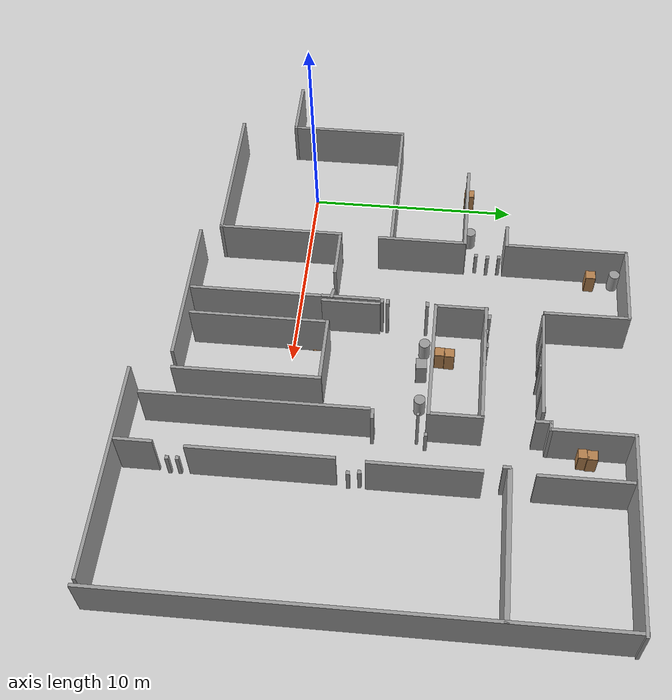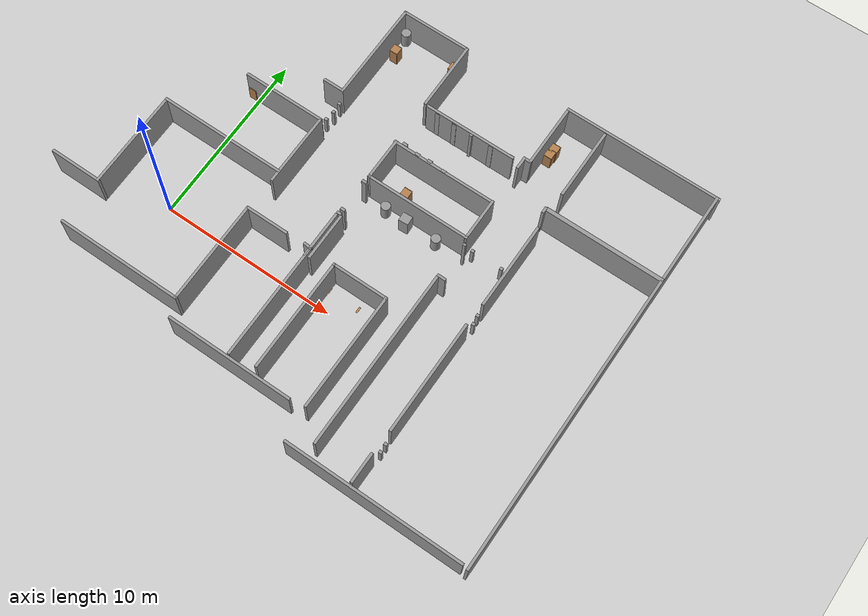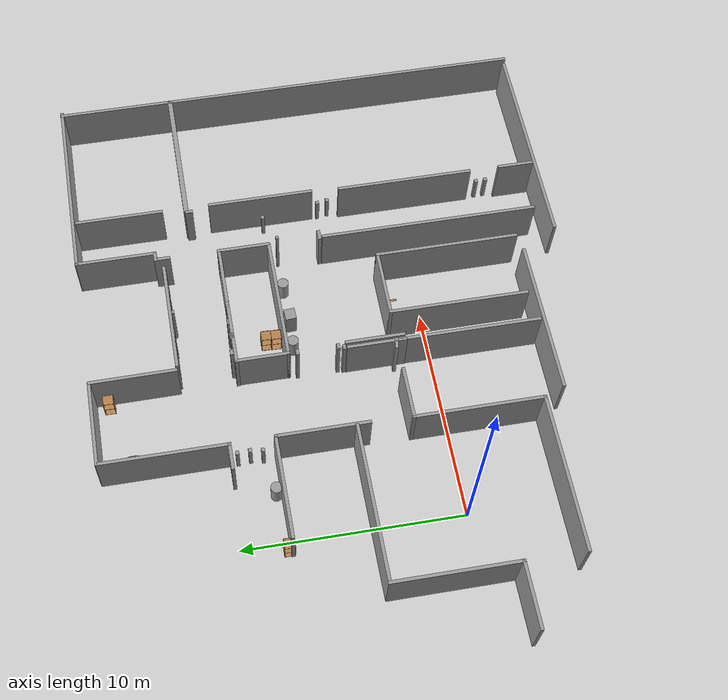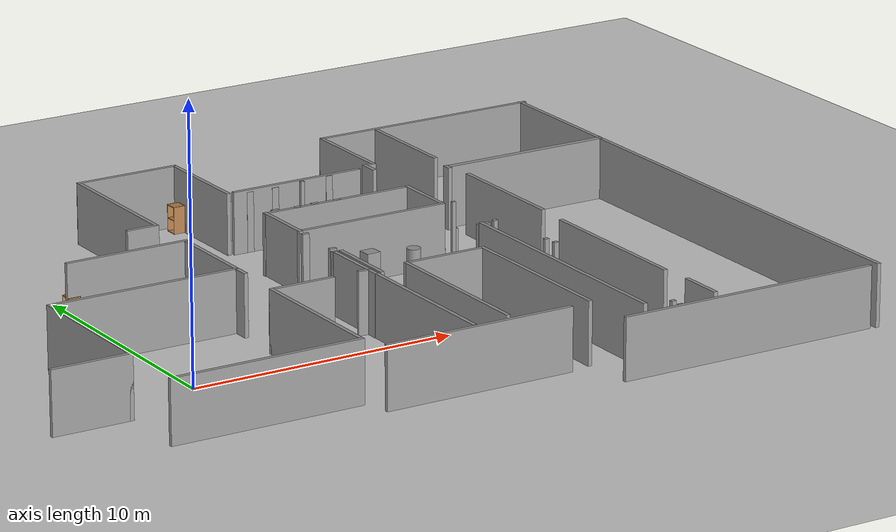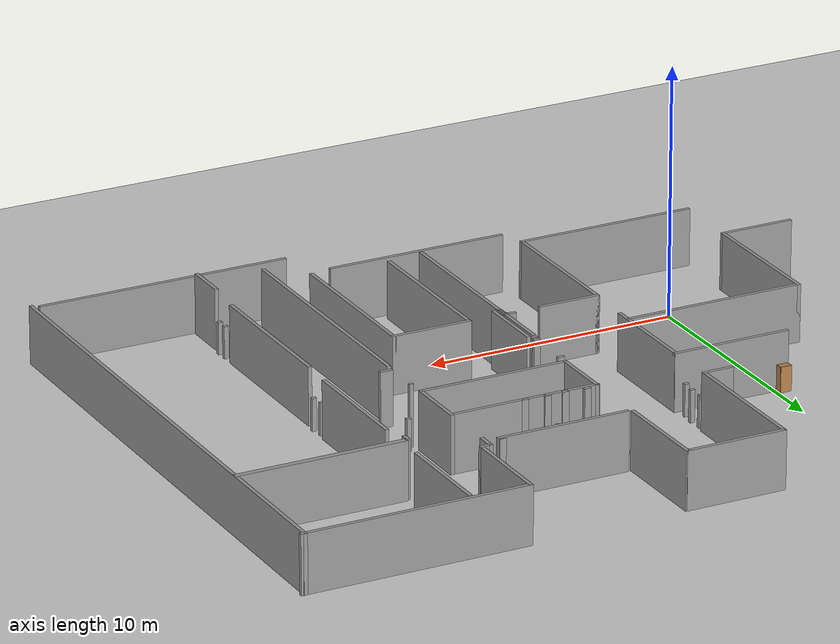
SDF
<sdf version="1.7">
 <world name="default">
  <light name="sun" type="directional">
   <pose>0 0 10 0 -0 0</pose>
   <diffuse>0.8 0.8 0.8 1</diffuse>
   <specular>0.2 0.2 0.2 1</specular>
   <attenuation>
    <range>1000</range>
    <constant>0.9</constant>
    <linear>0.01</linear>
    <quadratic>0.001</quadratic>
   </attenuation>
   <direction>-0.5 0.1 -0.9</direction>
   <spot><inner_angle>0</inner_angle><outer_angle>0</outer_angle><falloff>0</falloff></spot>
  </light>
  <model name="ground_plane">
   <static>1</static>
   <link name="link">
    <collision name="collision">
     <geometry><plane><normal>0 0 1</normal><size>100 100</size></plane></geometry>
     <surface>
      <contact><collide_bitmask>65535</collide_bitmask></contact>
      <friction><ode><mu>100</mu><mu2>50</mu2></ode></friction>
     </surface>
    </collision>
    <visual name="visual">
     <cast_shadows>0</cast_shadows>
     <geometry><plane><normal>0 0 1</normal><size>100 100</size></plane></geometry>
     <material>
      <script><uri>file://media/materials/scripts/gazebo.material</uri><name>Gazebo/Grey</name></script>
     </material>
    </visual>
   </link>
  </model>
  <gravity>0 0 -9.8</gravity>
  <magnetic_field>6e-06 2.3e-05 -4.2e-05</magnetic_field>
  <atmosphere type="adiabatic"/>
  <physics type="ode">
   <max_step_size>0.001</max_step_size>
   <real_time_factor>1</real_time_factor>
   <real_time_update_rate>1000</real_time_update_rate>
  </physics>
  <scene><ambient>0.4 0.4 0.4 1</ambient><background>0.7 0.7 0.7 1</background><shadows>1</shadows></scene>
  <spherical_coordinates>
   <surface_model>EARTH_WGS84</surface_model>
   <latitude_deg>0</latitude_deg>
   <longitude_deg>0</longitude_deg>
   <elevation>0</elevation>
   <heading_deg>0</heading_deg>
  </spherical_coordinates>
  <model name="cabinet">
   <static>1</static>
   <link name="cabinet_bottom_plate">
    <inertial>
     <pose>0 0 -1 0 -0 0</pose>
     <inertia><ixx>2.05</ixx><ixy>0</ixy><ixz>0</ixz><iyy>2.05</iyy><iyz>0</iyz><izz>2.05</izz></inertia>
     <mass>25</mass>
    </inertial>
    <collision name="cabinet_bottom_plate_geom">
     <pose>0 0 0.01 0 -0 0</pose>
     <geometry><box><size>0.45 0.45 0.02</size></box></geometry>
    </collision>
    <visual name="cabinet_bottom_plate_geom_visual">
     <pose>0 0 0.01 0 -0 0</pose>
     <geometry><box><size>0.45 0.45 0.02</size></box></geometry>
     <material>
      <script><uri>file://media/materials/scripts/gazebo.material</uri><name>Gazebo/Wood</name></script>
     </material>
    </visual>
    <collision name="cabinet_bottom_plate_geom_cabinet_back_plate">
     <pose>0.235 0 0.51 0 -0 0</pose>
     <geometry><box><size>0.02 0.45 1.02</size></box></geometry>
    </collision>
    <visual name="cabinet_bottom_plate_geom_cabinet_back_plate_visual">
     <pose>0.235 0 0.51 0 -0 0</pose>
     <geometry><box><size>0.02 0.45 1.02</size></box></geometry>
     <material>
      <script><uri>file://media/materials/scripts/gazebo.material</uri><name>Gazebo/Wood</name></script>
     </material>
    </visual>
    <collision name="cabinet_bottom_plate_geom_cabinet_left_plate">
     <pose>0 0.235 0.51 0 -0 0</pose>
     <geometry><box><size>0.45 0.02 1.02</size></box></geometry>
    </collision>
    <visual name="cabinet_bottom_plate_geom_cabinet_left_plate_visual">
     <pose>0 0.235 0.51 0 -0 0</pose>
     <geometry><box><size>0.45 0.02 1.02</size></box></geometry>
     <material>
      <script><uri>file://media/materials/scripts/gazebo.material</uri><name>Gazebo/Wood</name></script>
     </material>
    </visual>
    <collision name="cabinet_bottom_plate_geom_cabinet_middle_plate">
     <pose>0 0 0.51 0 -0 0</pose>
     <geometry><box><size>0.45 0.45 0.02</size></box></geometry>
    </collision>
    <visual name="cabinet_bottom_plate_geom_cabinet_middle_plate_visual">
     <pose>0 0 0.51 0 -0 0</pose>
     <geometry><box><size>0.45 0.45 0.02</size></box></geometry>
     <material>
      <script><uri>file://media/materials/scripts/gazebo.material</uri><name>Gazebo/Wood</name></script>
     </material>
    </visual>
    <collision name="cabinet_bottom_plate_geom_cabinet_right_plate">
     <pose>0 -0.235 0.51 0 -0 0</pose>
     <geometry><box><size>0.45 0.02 1.02</size></box></geometry>
    </collision>
    <visual name="cabinet_bottom_plate_geom_cabinet_right_plate_visual">
     <pose>0 -0.235 0.51 0 -0 0</pose>
     <geometry><box><size>0.45 0.02 1.02</size></box></geometry>
     <material>
      <script><uri>file://media/materials/scripts/gazebo.material</uri><name>Gazebo/Wood</name></script>
     </material>
    </visual>
    <collision name="cabinet_bottom_plate_geom_cabinet_top_plate">
     <pose>0 0 1.01 0 -0 0</pose>
     <geometry><box><size>0.45 0.45 0.02</size></box></geometry>
    </collision>
    <visual name="cabinet_bottom_plate_geom_cabinet_top_plate_visual">
     <pose>0 0 1.01 0 -0 0</pose>
     <geometry><box><size>0.45 0.45 0.02</size></box></geometry>
     <material>
      <script><uri>file://media/materials/scripts/gazebo.material</uri><name>Gazebo/Wood</name></script>
     </material>
    </visual>
   </link>
   <pose>9.66101 6.89219 0 0 -0 0</pose>
  </model>
  <model name="cabinet_0">
   <static>1</static>
   <link name="cabinet_bottom_plate">
    <inertial>
     <pose>0 0 -1 0 -0 0</pose>
     <inertia><ixx>2.05</ixx><ixy>0</ixy><ixz>0</ixz><iyy>2.05</iyy><iyz>0</iyz><izz>2.05</izz></inertia>
     <mass>25</mass>
    </inertial>
    <collision name="cabinet_bottom_plate_geom">
     <pose>0 0 0.01 0 -0 0</pose>
     <geometry><box><size>0.45 0.45 0.02</size></box></geometry>
    </collision>
    <visual name="cabinet_bottom_plate_geom_visual">
     <pose>0 0 0.01 0 -0 0</pose>
     <geometry><box><size>0.45 0.45 0.02</size></box></geometry>
     <material>
      <script><uri>file://media/materials/scripts/gazebo.material</uri><name>Gazebo/Wood</name></script>
     </material>
    </visual>
    <collision name="cabinet_bottom_plate_geom_cabinet_back_plate">
     <pose>0.235 0 0.51 0 -0 0</pose>
     <geometry><box><size>0.02 0.45 1.02</size></box></geometry>
    </collision>
    <visual name="cabinet_bottom_plate_geom_cabinet_back_plate_visual">
     <pose>0.235 0 0.51 0 -0 0</pose>
     <geometry><box><size>0.02 0.45 1.02</size></box></geometry>
     <material>
      <script><uri>file://media/materials/scripts/gazebo.material</uri><name>Gazebo/Wood</name></script>
     </material>
    </visual>
    <collision name="cabinet_bottom_plate_geom_cabinet_left_plate">
     <pose>0 0.235 0.51 0 -0 0</pose>
     <geometry><box><size>0.45 0.02 1.02</size></box></geometry>
    </collision>
    <visual name="cabinet_bottom_plate_geom_cabinet_left_plate_visual">
     <pose>0 0.235 0.51 0 -0 0</pose>
     <geometry><box><size>0.45 0.02 1.02</size></box></geometry>
     <material>
      <script><uri>file://media/materials/scripts/gazebo.material</uri><name>Gazebo/Wood</name></script>
     </material>
    </visual>
    <collision name="cabinet_bottom_plate_geom_cabinet_middle_plate">
     <pose>0 0 0.51 0 -0 0</pose>
     <geometry><box><size>0.45 0.45 0.02</size></box></geometry>
    </collision>
    <visual name="cabinet_bottom_plate_geom_cabinet_middle_plate_visual">
     <pose>0 0 0.51 0 -0 0</pose>
     <geometry><box><size>0.45 0.45 0.02</size></box></geometry>
     <material>
      <script><uri>file://media/materials/scripts/gazebo.material</uri><name>Gazebo/Wood</name></script>
     </material>
    </visual>
    <collision name="cabinet_bottom_plate_geom_cabinet_right_plate">
     <pose>0 -0.235 0.51 0 -0 0</pose>
     <geometry><box><size>0.45 0.02 1.02</size></box></geometry>
    </collision>
    <visual name="cabinet_bottom_plate_geom_cabinet_right_plate_visual">
     <pose>0 -0.235 0.51 0 -0 0</pose>
     <geometry><box><size>0.45 0.02 1.02</size></box></geometry>
     <material>
      <script><uri>file://media/materials/scripts/gazebo.material</uri><name>Gazebo/Wood</name></script>
     </material>
    </visual>
    <collision name="cabinet_bottom_plate_geom_cabinet_top_plate">
     <pose>0 0 1.01 0 -0 0</pose>
     <geometry><box><size>0.45 0.45 0.02</size></box></geometry>
    </collision>
    <visual name="cabinet_bottom_plate_geom_cabinet_top_plate_visual">
     <pose>0 0 1.01 0 -0 0</pose>
     <geometry><box><size>0.45 0.45 0.02</size></box></geometry>
     <material>
      <script><uri>file://media/materials/scripts/gazebo.material</uri><name>Gazebo/Wood</name></script>
     </material>
    </visual>
   </link>
   <pose>9.68381 7.3421 0 0 -0 0</pose>
  </model>
  <model name="wooden_board_clone">
   <link name="base">
    <pose>0 0 0.00523 0 -0 0</pose>
    <inertial>
     <mass>0.2765</mass>
     <inertia>
      <ixx>0.0025148</ixx>
      <ixy>0</ixy>
      <ixz>0</ixz>
      <iyy>0.00024037</iyy>
      <iyz>0</iyz>
      <izz>0.00275013</izz>
     </inertia>
    </inertial>
    <collision name="collision">
     <geometry><box><size>0.1016 0.3302 0.01046</size></box></geometry>
     <surface>
      <contact>
       <poissons_ratio>0.347</poissons_ratio>
       <elastic_modulus>8.8e+09</elastic_modulus>
       <ode><kp>100000</kp><kd>100</kd><max_vel>100</max_vel><min_depth>0.001</min_depth></ode>
      </contact>
      <friction>
       <torsional>
        <coefficient>1</coefficient>
        <use_patch_radius>0</use_patch_radius>
        <surface_radius>0.01</surface_radius>
       </torsional>
      </friction>
     </surface>
    </collision>
    <visual name="visual">
     <geometry><box><size>0.1016 0.3302 0.01046</size></box></geometry>
     <material>
      <script><uri>file://media/materials/scripts/gazebo.material</uri><name>Gazebo/Wood</name></script>
     </material>
    </visual>
    <visual name="tee_nut_1">
     <pose>0 -0.116 0 0 -0 0</pose>
     <geometry><cylinder><radius>0.00635</radius><length>0.0105646</length></cylinder></geometry>
     <material>
      <script><uri>file://media/materials/scripts/gazebo.material</uri><name>Gazebo/Grey</name></script>
     </material>
    </visual>
    <visual name="tee_nut_2">
     <pose>0 -0.038 0 0 -0 0</pose>
     <geometry><cylinder><radius>0.00635</radius><length>0.0105646</length></cylinder></geometry>
     <material>
      <script><uri>file://media/materials/scripts/gazebo.material</uri><name>Gazebo/Grey</name></script>
     </material>
    </visual>
    <visual name="tee_nut_3">
     <pose>0 0.038 0 0 -0 0</pose>
     <geometry><cylinder><radius>0.00635</radius><length>0.0105646</length></cylinder></geometry>
     <material>
      <script><uri>file://media/materials/scripts/gazebo.material</uri><name>Gazebo/Grey</name></script>
     </material>
    </visual>
    <visual name="tee_nut_4">
     <pose>0 0.116 0 0 -0 0</pose>
     <geometry><cylinder><radius>0.00635</radius><length>0.0105646</length></cylinder></geometry>
     <material>
      <script><uri>file://media/materials/scripts/gazebo.material</uri><name>Gazebo/Grey</name></script>
     </material>
    </visual>
   </link>
   <pose>9.26623 1.07105 -0.001007 0 -0 0.002678</pose>
  </model>
  <model name="wooden_board_clone_clone">
   <link name="base">
    <pose>0 0 0.00523 0 -0 0</pose>
    <inertial>
     <mass>0.2765</mass>
     <inertia>
      <ixx>0.0025148</ixx>
      <ixy>0</ixy>
      <ixz>0</ixz>
      <iyy>0.00024037</iyy>
      <iyz>0</iyz>
      <izz>0.00275013</izz>
     </inertia>
    </inertial>
    <collision name="collision">
     <geometry><box><size>0.1016 0.3302 0.01046</size></box></geometry>
     <surface>
      <contact>
       <poissons_ratio>0.347</poissons_ratio>
       <elastic_modulus>8.8e+09</elastic_modulus>
       <ode><kp>100000</kp><kd>100</kd><max_vel>100</max_vel><min_depth>0.001</min_depth></ode>
      </contact>
      <friction>
       <torsional>
        <coefficient>1</coefficient>
        <use_patch_radius>0</use_patch_radius>
        <surface_radius>0.01</surface_radius>
       </torsional>
      </friction>
     </surface>
    </collision>
    <visual name="visual">
     <geometry><box><size>0.1016 0.3302 0.01046</size></box></geometry>
     <material>
      <script><uri>file://media/materials/scripts/gazebo.material</uri><name>Gazebo/Wood</name></script>
     </material>
    </visual>
    <visual name="tee_nut_1">
     <pose>0 -0.116 0 0 -0 0</pose>
     <geometry><cylinder><radius>0.00635</radius><length>0.0105646</length></cylinder></geometry>
     <material>
      <script><uri>file://media/materials/scripts/gazebo.material</uri><name>Gazebo/Grey</name></script>
     </material>
    </visual>
    <visual name="tee_nut_2">
     <pose>0 -0.038 0 0 -0 0</pose>
     <geometry><cylinder><radius>0.00635</radius><length>0.0105646</length></cylinder></geometry>
     <material>
      <script><uri>file://media/materials/scripts/gazebo.material</uri><name>Gazebo/Grey</name></script>
     </material>
    </visual>
    <visual name="tee_nut_3">
     <pose>0 0.038 0 0 -0 0</pose>
     <geometry><cylinder><radius>0.00635</radius><length>0.0105646</length></cylinder></geometry>
     <material>
      <script><uri>file://media/materials/scripts/gazebo.material</uri><name>Gazebo/Grey</name></script>
     </material>
    </visual>
    <visual name="tee_nut_4">
     <pose>0 0.116 0 0 -0 0</pose>
     <geometry><cylinder><radius>0.00635</radius><length>0.0105646</length></cylinder></geometry>
     <material>
      <script><uri>file://media/materials/scripts/gazebo.material</uri><name>Gazebo/Grey</name></script>
     </material>
    </visual>
   </link>
   <pose>9.37039 1.07358 -0.001007 0 -0 0.002678</pose>
  </model>
  <model name="wooden_board_clone_clone_1">
   <link name="base">
    <pose>0 0 0.00523 0 -0 0</pose>
    <inertial>
     <mass>0.2765</mass>
     <inertia>
      <ixx>0.0025148</ixx>
      <ixy>0</ixy>
      <ixz>0</ixz>
      <iyy>0.00024037</iyy>
      <iyz>0</iyz>
      <izz>0.00275013</izz>
     </inertia>
    </inertial>
    <collision name="collision">
     <geometry><box><size>0.1016 0.3302 0.01046</size></box></geometry>
     <surface>
      <contact>
       <poissons_ratio>0.347</poissons_ratio>
       <elastic_modulus>8.8e+09</elastic_modulus>
       <ode><kp>100000</kp><kd>100</kd><max_vel>100</max_vel><min_depth>0.001</min_depth></ode>
      </contact>
      <friction>
       <torsional>
        <coefficient>1</coefficient>
        <use_patch_radius>0</use_patch_radius>
        <surface_radius>0.01</surface_radius>
       </torsional>
      </friction>
     </surface>
    </collision>
    <visual name="visual">
     <geometry><box><size>0.1016 0.3302 0.01046</size></box></geometry>
     <material>
      <script><uri>file://media/materials/scripts/gazebo.material</uri><name>Gazebo/Wood</name></script>
     </material>
    </visual>
    <visual name="tee_nut_1">
     <pose>0 -0.116 0 0 -0 0</pose>
     <geometry><cylinder><radius>0.00635</radius><length>0.0105646</length></cylinder></geometry>
     <material>
      <script><uri>file://media/materials/scripts/gazebo.material</uri><name>Gazebo/Grey</name></script>
     </material>
    </visual>
    <visual name="tee_nut_2">
     <pose>0 -0.038 0 0 -0 0</pose>
     <geometry><cylinder><radius>0.00635</radius><length>0.0105646</length></cylinder></geometry>
     <material>
      <script><uri>file://media/materials/scripts/gazebo.material</uri><name>Gazebo/Grey</name></script>
     </material>
    </visual>
    <visual name="tee_nut_3">
     <pose>0 0.038 0 0 -0 0</pose>
     <geometry><cylinder><radius>0.00635</radius><length>0.0105646</length></cylinder></geometry>
     <material>
      <script><uri>file://media/materials/scripts/gazebo.material</uri><name>Gazebo/Grey</name></script>
     </material>
    </visual>
    <visual name="tee_nut_4">
     <pose>0 0.116 0 0 -0 0</pose>
     <geometry><cylinder><radius>0.00635</radius><length>0.0105646</length></cylinder></geometry>
     <material>
      <script><uri>file://media/materials/scripts/gazebo.material</uri><name>Gazebo/Grey</name></script>
     </material>
    </visual>
   </link>
   <pose>11.1431 1.04865 -0.001007 0 -0 0.002631</pose>
  </model>
  <model name="cabinet_clone_1">
   <static>1</static>
   <link name="cabinet_bottom_plate">
    <inertial>
     <pose>0 0 -1 0 -0 0</pose>
     <inertia><ixx>2.05</ixx><ixy>0</ixy><ixz>0</ixz><iyy>2.05</iyy><iyz>0</iyz><izz>2.05</izz></inertia>
     <mass>25</mass>
    </inertial>
    <collision name="cabinet_bottom_plate_geom">
     <pose>0 0 0.01 0 -0 0</pose>
     <geometry><box><size>0.45 0.45 0.02</size></box></geometry>
    </collision>
    <visual name="cabinet_bottom_plate_geom_visual">
     <pose>0 0 0.01 0 -0 0</pose>
     <geometry><box><size>0.45 0.45 0.02</size></box></geometry>
     <material>
      <script><uri>file://media/materials/scripts/gazebo.material</uri><name>Gazebo/Wood</name></script>
     </material>
    </visual>
    <collision name="cabinet_bottom_plate_geom_cabinet_back_plate">
     <pose>0.235 0 0.51 0 -0 0</pose>
     <geometry><box><size>0.02 0.45 1.02</size></box></geometry>
    </collision>
    <visual name="cabinet_bottom_plate_geom_cabinet_back_plate_visual">
     <pose>0.235 0 0.51 0 -0 0</pose>
     <geometry><box><size>0.02 0.45 1.02</size></box></geometry>
     <material>
      <script><uri>file://media/materials/scripts/gazebo.material</uri><name>Gazebo/Wood</name></script>
     </material>
    </visual>
    <collision name="cabinet_bottom_plate_geom_cabinet_left_plate">
     <pose>0 0.235 0.51 0 -0 0</pose>
     <geometry><box><size>0.45 0.02 1.02</size></box></geometry>
    </collision>
    <visual name="cabinet_bottom_plate_geom_cabinet_left_plate_visual">
     <pose>0 0.235 0.51 0 -0 0</pose>
     <geometry><box><size>0.45 0.02 1.02</size></box></geometry>
     <material>
      <script><uri>file://media/materials/scripts/gazebo.material</uri><name>Gazebo/Wood</name></script>
     </material>
    </visual>
    <collision name="cabinet_bottom_plate_geom_cabinet_middle_plate">
     <pose>0 0 0.51 0 -0 0</pose>
     <geometry><box><size>0.45 0.45 0.02</size></box></geometry>
    </collision>
    <visual name="cabinet_bottom_plate_geom_cabinet_middle_plate_visual">
     <pose>0 0 0.51 0 -0 0</pose>
     <geometry><box><size>0.45 0.45 0.02</size></box></geometry>
     <material>
      <script><uri>file://media/materials/scripts/gazebo.material</uri><name>Gazebo/Wood</name></script>
     </material>
    </visual>
    <collision name="cabinet_bottom_plate_geom_cabinet_right_plate">
     <pose>0 -0.235 0.51 0 -0 0</pose>
     <geometry><box><size>0.45 0.02 1.02</size></box></geometry>
    </collision>
    <visual name="cabinet_bottom_plate_geom_cabinet_right_plate_visual">
     <pose>0 -0.235 0.51 0 -0 0</pose>
     <geometry><box><size>0.45 0.02 1.02</size></box></geometry>
     <material>
      <script><uri>file://media/materials/scripts/gazebo.material</uri><name>Gazebo/Wood</name></script>
     </material>
    </visual>
    <collision name="cabinet_bottom_plate_geom_cabinet_top_plate">
     <pose>0 0 1.01 0 -0 0</pose>
     <geometry><box><size>0.45 0.45 0.02</size></box></geometry>
    </collision>
    <visual name="cabinet_bottom_plate_geom_cabinet_top_plate_visual">
     <pose>0 0 1.01 0 -0 0</pose>
     <geometry><box><size>0.45 0.45 0.02</size></box></geometry>
     <material>
      <script><uri>file://media/materials/scripts/gazebo.material</uri><name>Gazebo/Wood</name></script>
     </material>
    </visual>
   </link>
   <pose>-0.359128 7.87917 0 0 -0 0</pose>
  </model>
  <model name="unit_cylinder_0_clone_1">
   <pose>2.24031 8.02243 0.499998 1e-06 1e-06 1e-06</pose>
   <link name="link">
    <inertial>
     <mass>1</mass>
     <inertia><ixx>0.145833</ixx><ixy>0</ixy><ixz>0</ixz><iyy>0.145833</iyy><iyz>0</iyz><izz>0.125</izz></inertia>
    </inertial>
    <collision name="collision">
     <geometry><cylinder><radius>0.25828</radius><length>1</length></cylinder></geometry>
    </collision>
    <visual name="visual">
     <geometry><cylinder><radius>0.25828</radius><length>1</length></cylinder></geometry>
     <material>
      <script><name>Gazebo/Grey</name><uri>file://media/materials/scripts/gazebo.material</uri></script>
     </material>
    </visual>
   </link>
  </model>
  <model name="rastech_map_02">
   <link name="Wall_14">
    <pose>-2.58274 10.4706 0 0 -0 0</pose>
    <visual name="Wall_14_Visual">
     <pose>0 0 1.25 0 -0 0</pose>
     <geometry><box><size>4 0.15 2.5</size></box></geometry>
     <material>
      <script><uri>file://media/materials/scripts/gazebo.material</uri><name>Gazebo/Grey</name></script>
      <ambient>1 1 1 1</ambient>
      <shader type="pixel"/>
     </material>
     <meta><layer>0</layer></meta>
    </visual>
    <collision name="Wall_14_Collision">
     <pose>0 0 1.25 0 -0 0</pose>
     <geometry><box><size>4 0.15 2.5</size></box></geometry>
     <surface>
      <friction>
       <ode><mu>1</mu><mu2>1</mu2><fdir1>0 0 0</fdir1><slip1>0</slip1><slip2>0</slip2></ode>
       <torsional>
        <coefficient>1</coefficient>
        <patch_radius>0</patch_radius>
        <surface_radius>0</surface_radius>
        <use_patch_radius>1</use_patch_radius>
        <ode><slip>0</slip></ode>
       </torsional>
      </friction>
      <bounce><restitution_coefficient>0</restitution_coefficient><threshold>1e+06</threshold></bounce>
      <contact>
       <collide_without_contact>0</collide_without_contact>
       <collide_without_contact_bitmask>1</collide_without_contact_bitmask>
       <collide_bitmask>1</collide_bitmask>
       <ode>
        <soft_cfm>0</soft_cfm>
        <soft_erp>0.2</soft_erp>
        <kp>1e+13</kp>
        <kd>1</kd>
        <max_vel>0.01</max_vel>
        <min_depth>0</min_depth>
       </ode>
       <bullet>
        <split_impulse>1</split_impulse>
        <split_impulse_penetration_threshold>-0.01</split_impulse_penetration_threshold>
        <soft_cfm>0</soft_cfm>
        <soft_erp>0.2</soft_erp>
        <kp>1e+13</kp>
        <kd>1</kd>
       </bullet>
      </contact>
     </surface>
    </collision>
   </link>
   <link name="Wall_18">
    <pose>-0.701383 -2.43126 0 0 -0 1.5708</pose>
    <visual name="Wall_18_Visual">
     <pose>0 0 1.25 0 -0 0</pose>
     <geometry><box><size>2.75 0.15 2.5</size></box></geometry>
     <material>
      <script><uri>file://media/materials/scripts/gazebo.material</uri><name>Gazebo/Grey</name></script>
      <ambient>1 1 1 1</ambient>
      <shader type="pixel"/>
     </material>
     <meta><layer>0</layer></meta>
    </visual>
    <collision name="Wall_18_Collision">
     <pose>0 0 1.25 0 -0 0</pose>
     <geometry><box><size>2.75 0.15 2.5</size></box></geometry>
     <surface>
      <friction>
       <ode><mu>1</mu><mu2>1</mu2><fdir1>0 0 0</fdir1><slip1>0</slip1><slip2>0</slip2></ode>
       <torsional>
        <coefficient>1</coefficient>
        <patch_radius>0</patch_radius>
        <surface_radius>0</surface_radius>
        <use_patch_radius>1</use_patch_radius>
        <ode><slip>0</slip></ode>
       </torsional>
      </friction>
      <bounce><restitution_coefficient>0</restitution_coefficient><threshold>1e+06</threshold></bounce>
      <contact>
       <collide_without_contact>0</collide_without_contact>
       <collide_without_contact_bitmask>1</collide_without_contact_bitmask>
       <collide_bitmask>1</collide_bitmask>
       <ode>
        <soft_cfm>0</soft_cfm>
        <soft_erp>0.2</soft_erp>
        <kp>1e+13</kp>
        <kd>1</kd>
        <max_vel>0.01</max_vel>
        <min_depth>0</min_depth>
       </ode>
       <bullet>
        <split_impulse>1</split_impulse>
        <split_impulse_penetration_threshold>-0.01</split_impulse_penetration_threshold>
        <soft_cfm>0</soft_cfm>
        <soft_erp>0.2</soft_erp>
        <kp>1e+13</kp>
        <kd>1</kd>
       </bullet>
      </contact>
     </surface>
    </collision>
   </link>
   <link name="Wall_19">
    <pose>-0.645492 -0.952282 -0.032873 0 -0 0</pose>
    <visual name="Wall_19_Visual">
     <pose>0 0 1.25 0 -0 0</pose>
     <geometry><box><size>0.25 0.15 2.5</size></box></geometry>
     <material>
      <script><uri>file://media/materials/scripts/gazebo.material</uri><name>Gazebo/Grey</name></script>
      <ambient>1 1 1 1</ambient>
      <shader type="pixel"/>
     </material>
     <meta><layer>0</layer></meta>
    </visual>
    <collision name="Wall_19_Collision">
     <pose>0 0 1.25 0 -0 0</pose>
     <geometry><box><size>0.25 0.15 2.5</size></box></geometry>
     <surface>
      <friction>
       <ode><mu>1</mu><mu2>1</mu2><fdir1>0 0 0</fdir1><slip1>0</slip1><slip2>0</slip2></ode>
       <torsional>
        <coefficient>1</coefficient>
        <patch_radius>0</patch_radius>
        <surface_radius>0</surface_radius>
        <use_patch_radius>1</use_patch_radius>
        <ode><slip>0</slip></ode>
       </torsional>
      </friction>
      <bounce><restitution_coefficient>0</restitution_coefficient><threshold>1e+06</threshold></bounce>
      <contact>
       <collide_without_contact>0</collide_without_contact>
       <collide_without_contact_bitmask>1</collide_without_contact_bitmask>
       <collide_bitmask>1</collide_bitmask>
       <ode>
        <soft_cfm>0</soft_cfm>
        <soft_erp>0.2</soft_erp>
        <kp>1e+13</kp>
        <kd>1</kd>
        <max_vel>0.01</max_vel>
        <min_depth>0</min_depth>
       </ode>
       <bullet>
        <split_impulse>1</split_impulse>
        <split_impulse_penetration_threshold>-0.01</split_impulse_penetration_threshold>
        <soft_cfm>0</soft_cfm>
        <soft_erp>0.2</soft_erp>
        <kp>1e+13</kp>
        <kd>1</kd>
       </bullet>
      </contact>
     </surface>
    </collision>
   </link>
   <link name="Wall_21">
    <pose>-0.450715 -2.39462 0 0 0 -1.5708</pose>
    <visual name="Wall_21_Visual">
     <pose>0 0 1.25 0 -0 0</pose>
     <geometry><box><size>2.75 0.15 2.5</size></box></geometry>
     <material>
      <script><uri>file://media/materials/scripts/gazebo.material</uri><name>Gazebo/Grey</name></script>
      <ambient>1 1 1 1</ambient>
      <shader type="pixel"/>
     </material>
     <meta><layer>0</layer></meta>
    </visual>
    <collision name="Wall_21_Collision">
     <pose>0 0 1.25 0 -0 0</pose>
     <geometry><box><size>2.75 0.15 2.5</size></box></geometry>
     <surface>
      <friction>
       <ode><mu>1</mu><mu2>1</mu2><fdir1>0 0 0</fdir1><slip1>0</slip1><slip2>0</slip2></ode>
       <torsional>
        <coefficient>1</coefficient>
        <patch_radius>0</patch_radius>
        <surface_radius>0</surface_radius>
        <use_patch_radius>1</use_patch_radius>
        <ode><slip>0</slip></ode>
       </torsional>
      </friction>
      <bounce><restitution_coefficient>0</restitution_coefficient><threshold>1e+06</threshold></bounce>
      <contact>
       <collide_without_contact>0</collide_without_contact>
       <collide_without_contact_bitmask>1</collide_without_contact_bitmask>
       <collide_bitmask>1</collide_bitmask>
       <ode>
        <soft_cfm>0</soft_cfm>
        <soft_erp>0.2</soft_erp>
        <kp>1e+13</kp>
        <kd>1</kd>
        <max_vel>0.01</max_vel>
        <min_depth>0</min_depth>
       </ode>
       <bullet>
        <split_impulse>1</split_impulse>
        <split_impulse_penetration_threshold>-0.01</split_impulse_penetration_threshold>
        <soft_cfm>0</soft_cfm>
        <soft_erp>0.2</soft_erp>
        <kp>1e+13</kp>
        <kd>1</kd>
       </bullet>
      </contact>
     </surface>
    </collision>
   </link>
   <link name="Wall_23">
    <pose>-0.566645 2.73832 0 0 0 -1.5708</pose>
    <visual name="Wall_23_Visual">
     <pose>0 0 1.25 0 -0 0</pose>
     <geometry><box><size>2.5 0.15 2.5</size></box></geometry>
     <material>
      <script><uri>file://media/materials/scripts/gazebo.material</uri><name>Gazebo/Grey</name></script>
      <ambient>1 1 1 1</ambient>
      <shader type="pixel"/>
     </material>
     <meta><layer>0</layer></meta>
    </visual>
    <collision name="Wall_23_Collision">
     <pose>0 0 1.25 0 -0 0</pose>
     <geometry><box><size>2.5 0.15 2.5</size></box></geometry>
     <surface>
      <friction>
       <ode><mu>1</mu><mu2>1</mu2><fdir1>0 0 0</fdir1><slip1>0</slip1><slip2>0</slip2></ode>
       <torsional>
        <coefficient>1</coefficient>
        <patch_radius>0</patch_radius>
        <surface_radius>0</surface_radius>
        <use_patch_radius>1</use_patch_radius>
        <ode><slip>0</slip></ode>
       </torsional>
      </friction>
      <bounce><restitution_coefficient>0</restitution_coefficient><threshold>1e+06</threshold></bounce>
      <contact>
       <collide_without_contact>0</collide_without_contact>
       <collide_without_contact_bitmask>1</collide_without_contact_bitmask>
       <collide_bitmask>1</collide_bitmask>
       <ode>
        <soft_cfm>0</soft_cfm>
        <soft_erp>0.2</soft_erp>
        <kp>1e+13</kp>
        <kd>1</kd>
        <max_vel>0.01</max_vel>
        <min_depth>0</min_depth>
       </ode>
       <bullet>
        <split_impulse>1</split_impulse>
        <split_impulse_penetration_threshold>-0.01</split_impulse_penetration_threshold>
        <soft_cfm>0</soft_cfm>
        <soft_erp>0.2</soft_erp>
        <kp>1e+13</kp>
        <kd>1</kd>
       </bullet>
      </contact>
     </surface>
    </collision>
   </link>
   <link name="Wall_25">
    <pose>2.35835 1.56332 0 0 -0 0</pose>
    <visual name="Wall_25_Visual">
     <pose>0 0 1.25 0 -0 0</pose>
     <geometry><box><size>6 0.15 2.5</size></box></geometry>
     <material>
      <script><uri>file://media/materials/scripts/gazebo.material</uri><name>Gazebo/Grey</name></script>
      <ambient>1 1 1 1</ambient>
      <shader type="pixel"/>
     </material>
     <meta><layer>0</layer></meta>
    </visual>
    <collision name="Wall_25_Collision">
     <pose>0 0 1.25 0 -0 0</pose>
     <geometry><box><size>6 0.15 2.5</size></box></geometry>
     <surface>
      <friction>
       <ode><mu>1</mu><mu2>1</mu2><fdir1>0 0 0</fdir1><slip1>0</slip1><slip2>0</slip2></ode>
       <torsional>
        <coefficient>1</coefficient>
        <patch_radius>0</patch_radius>
        <surface_radius>0</surface_radius>
        <use_patch_radius>1</use_patch_radius>
        <ode><slip>0</slip></ode>
       </torsional>
      </friction>
      <bounce><restitution_coefficient>0</restitution_coefficient><threshold>1e+06</threshold></bounce>
      <contact>
       <collide_without_contact>0</collide_without_contact>
       <collide_without_contact_bitmask>1</collide_without_contact_bitmask>
       <collide_bitmask>1</collide_bitmask>
       <ode>
        <soft_cfm>0</soft_cfm>
        <soft_erp>0.2</soft_erp>
        <kp>1e+13</kp>
        <kd>1</kd>
        <max_vel>0.01</max_vel>
        <min_depth>0</min_depth>
       </ode>
       <bullet>
        <split_impulse>1</split_impulse>
        <split_impulse_penetration_threshold>-0.01</split_impulse_penetration_threshold>
        <soft_cfm>0</soft_cfm>
        <soft_erp>0.2</soft_erp>
        <kp>1e+13</kp>
        <kd>1</kd>
       </bullet>
      </contact>
     </surface>
    </collision>
   </link>
   <link name="Wall_26">
    <pose>5.28336 2.73832 0 0 -0 1.5708</pose>
    <visual name="Wall_26_Visual">
     <pose>0 0 1.25 0 -0 0</pose>
     <geometry><box><size>2.5 0.15 2.5</size></box></geometry>
     <material>
      <script><uri>file://media/materials/scripts/gazebo.material</uri><name>Gazebo/Grey</name></script>
      <ambient>1 1 1 1</ambient>
      <shader type="pixel"/>
     </material>
     <meta><layer>0</layer></meta>
    </visual>
    <collision name="Wall_26_Collision">
     <pose>0 0 1.25 0 -0 0</pose>
     <geometry><box><size>2.5 0.15 2.5</size></box></geometry>
     <surface>
      <friction>
       <ode><mu>1</mu><mu2>1</mu2><fdir1>0 0 0</fdir1><slip1>0</slip1><slip2>0</slip2></ode>
       <torsional>
        <coefficient>1</coefficient>
        <patch_radius>0</patch_radius>
        <surface_radius>0</surface_radius>
        <use_patch_radius>1</use_patch_radius>
        <ode><slip>0</slip></ode>
       </torsional>
      </friction>
      <bounce><restitution_coefficient>0</restitution_coefficient><threshold>1e+06</threshold></bounce>
      <contact>
       <collide_without_contact>0</collide_without_contact>
       <collide_without_contact_bitmask>1</collide_without_contact_bitmask>
       <collide_bitmask>1</collide_bitmask>
       <ode>
        <soft_cfm>0</soft_cfm>
        <soft_erp>0.2</soft_erp>
        <kp>1e+13</kp>
        <kd>1</kd>
        <max_vel>0.01</max_vel>
        <min_depth>0</min_depth>
       </ode>
       <bullet>
        <split_impulse>1</split_impulse>
        <split_impulse_penetration_threshold>-0.01</split_impulse_penetration_threshold>
        <soft_cfm>0</soft_cfm>
        <soft_erp>0.2</soft_erp>
        <kp>1e+13</kp>
        <kd>1</kd>
       </bullet>
      </contact>
     </surface>
    </collision>
   </link>
   <link name="Wall_27">
    <pose>2.35835 3.91332 0 0 -0 3.14159</pose>
    <inertial>
     <inertia><ixx>0</ixx><ixy>0</ixy><ixz>0</ixz><iyy>0</iyy><iyz>0</iyz><izz>0</izz></inertia>
     <mass>0</mass>
    </inertial>
    <visual name="Wall_27_Visual">
     <pose>0 0 1.25 0 -0 0</pose>
     <geometry><box><size>0.265883 0.15 2.5</size></box></geometry>
     <material>
      <script><uri>file://media/materials/scripts/gazebo.material</uri><name>Gazebo/Grey</name></script>
      <ambient>1 1 1 1</ambient>
      <shader type="pixel"/>
     </material>
     <meta><layer>0</layer></meta>
    </visual>
    <collision name="Wall_27_Collision">
     <pose>0 0 1.25 0 -0 0</pose>
     <geometry><box><size>0.265883 0.15 2.5</size></box></geometry>
     <surface>
      <friction>
       <ode><mu>1</mu><mu2>1</mu2><fdir1>0 0 0</fdir1><slip1>0</slip1><slip2>0</slip2></ode>
       <torsional>
        <coefficient>1</coefficient>
        <patch_radius>0</patch_radius>
        <surface_radius>0</surface_radius>
        <use_patch_radius>1</use_patch_radius>
        <ode><slip>0</slip></ode>
       </torsional>
      </friction>
      <bounce><restitution_coefficient>0</restitution_coefficient><threshold>1e+06</threshold></bounce>
      <contact>
       <collide_without_contact>0</collide_without_contact>
       <collide_without_contact_bitmask>1</collide_without_contact_bitmask>
       <collide_bitmask>1</collide_bitmask>
       <ode>
        <soft_cfm>0</soft_cfm>
        <soft_erp>0.2</soft_erp>
        <kp>1e+13</kp>
        <kd>1</kd>
        <max_vel>0.01</max_vel>
        <min_depth>0</min_depth>
       </ode>
       <bullet>
        <split_impulse>1</split_impulse>
        <split_impulse_penetration_threshold>-0.01</split_impulse_penetration_threshold>
        <soft_cfm>0</soft_cfm>
        <soft_erp>0.2</soft_erp>
        <kp>1e+13</kp>
        <kd>1</kd>
       </bullet>
      </contact>
     </surface>
    </collision>
   </link>
   <link name="Wall_27_clone">
    <pose>0.733131 3.94617 0 0 -0 3.14159</pose>
    <inertial>
     <inertia><ixx>0</ixx><ixy>0</ixy><ixz>0</ixz><iyy>0</iyy><iyz>0</iyz><izz>0</izz></inertia>
     <mass>0</mass>
    </inertial>
    <visual name="Wall_27_Visual">
     <pose>0 0 1.25 0 -0 0</pose>
     <geometry><box><size>0.265883 0.15 2.5</size></box></geometry>
     <material>
      <script><uri>file://media/materials/scripts/gazebo.material</uri><name>Gazebo/Grey</name></script>
      <ambient>1 1 1 1</ambient>
      <shader type="pixel"/>
     </material>
     <meta><layer>0</layer></meta>
    </visual>
    <collision name="Wall_27_Collision">
     <pose>0 0 1.25 0 -0 0</pose>
     <geometry><box><size>0.265883 0.15 2.5</size></box></geometry>
     <surface>
      <friction>
       <ode><mu>1</mu><mu2>1</mu2><fdir1>0 0 0</fdir1><slip1>0</slip1><slip2>0</slip2></ode>
       <torsional>
        <coefficient>1</coefficient>
        <patch_radius>0</patch_radius>
        <surface_radius>0</surface_radius>
        <use_patch_radius>1</use_patch_radius>
        <ode><slip>0</slip></ode>
       </torsional>
      </friction>
      <bounce><restitution_coefficient>0</restitution_coefficient><threshold>1e+06</threshold></bounce>
      <contact>
       <collide_without_contact>0</collide_without_contact>
       <collide_without_contact_bitmask>1</collide_without_contact_bitmask>
       <collide_bitmask>1</collide_bitmask>
       <ode>
        <soft_cfm>0</soft_cfm>
        <soft_erp>0.2</soft_erp>
        <kp>1e+13</kp>
        <kd>1</kd>
        <max_vel>0.01</max_vel>
        <min_depth>0</min_depth>
       </ode>
       <bullet>
        <split_impulse>1</split_impulse>
        <split_impulse_penetration_threshold>-0.01</split_impulse_penetration_threshold>
        <soft_cfm>0</soft_cfm>
        <soft_erp>0.2</soft_erp>
        <kp>1e+13</kp>
        <kd>1</kd>
       </bullet>
      </contact>
     </surface>
    </collision>
   </link>
   <link name="Wall_27_clone_0">
    <pose>2.29874 3.89981 0 0 -0 3.14159</pose>
    <inertial>
     <inertia><ixx>0</ixx><ixy>0</ixy><ixz>0</ixz><iyy>0</iyy><iyz>0</iyz><izz>0</izz></inertia>
     <mass>0</mass>
    </inertial>
    <visual name="Wall_27_Visual">
     <pose>0 0 1.25 0 -0 0</pose>
     <geometry><box><size>5.95009 0.15 2.5</size></box></geometry>
     <material>
      <script><uri>file://media/materials/scripts/gazebo.material</uri><name>Gazebo/Grey</name></script>
      <ambient>1 1 1 1</ambient>
      <shader type="pixel"/>
     </material>
     <meta><layer>0</layer></meta>
    </visual>
    <collision name="Wall_27_Collision">
     <pose>0 0 1.25 0 -0 0</pose>
     <geometry><box><size>5.95009 0.15 2.5</size></box></geometry>
     <surface>
      <friction>
       <ode><mu>1</mu><mu2>1</mu2><fdir1>0 0 0</fdir1><slip1>0</slip1><slip2>0</slip2></ode>
       <torsional>
        <coefficient>1</coefficient>
        <patch_radius>0</patch_radius>
        <surface_radius>0</surface_radius>
        <use_patch_radius>1</use_patch_radius>
        <ode><slip>0</slip></ode>
       </torsional>
      </friction>
      <bounce><restitution_coefficient>0</restitution_coefficient><threshold>1e+06</threshold></bounce>
      <contact>
       <collide_without_contact>0</collide_without_contact>
       <collide_without_contact_bitmask>1</collide_without_contact_bitmask>
       <collide_bitmask>1</collide_bitmask>
       <ode>
        <soft_cfm>0</soft_cfm>
        <soft_erp>0.2</soft_erp>
        <kp>1e+13</kp>
        <kd>1</kd>
        <max_vel>0.01</max_vel>
        <min_depth>0</min_depth>
       </ode>
       <bullet>
        <split_impulse>1</split_impulse>
        <split_impulse_penetration_threshold>-0.01</split_impulse_penetration_threshold>
        <soft_cfm>0</soft_cfm>
        <soft_erp>0.2</soft_erp>
        <kp>1e+13</kp>
        <kd>1</kd>
       </bullet>
      </contact>
     </surface>
    </collision>
   </link>
   <link name="Wall_27_clone_1">
    <pose>1.46486 3.97748 0 0 -0 3.14159</pose>
    <inertial>
     <inertia><ixx>0</ixx><ixy>0</ixy><ixz>0</ixz><iyy>0</iyy><iyz>0</iyz><izz>0</izz></inertia>
     <mass>0</mass>
    </inertial>
    <visual name="Wall_27_Visual">
     <pose>0 0 1.25 0 -0 0</pose>
     <geometry><box><size>0.265883 0.15 2.5</size></box></geometry>
     <material>
      <script><uri>file://media/materials/scripts/gazebo.material</uri><name>Gazebo/Grey</name></script>
      <ambient>1 1 1 1</ambient>
      <shader type="pixel"/>
     </material>
     <meta><layer>0</layer></meta>
    </visual>
    <collision name="Wall_27_Collision">
     <pose>0 0 1.25 0 -0 0</pose>
     <geometry><box><size>0.265883 0.15 2.5</size></box></geometry>
     <surface>
      <friction>
       <ode><mu>1</mu><mu2>1</mu2><fdir1>0 0 0</fdir1><slip1>0</slip1><slip2>0</slip2></ode>
       <torsional>
        <coefficient>1</coefficient>
        <patch_radius>0</patch_radius>
        <surface_radius>0</surface_radius>
        <use_patch_radius>1</use_patch_radius>
        <ode><slip>0</slip></ode>
       </torsional>
      </friction>
      <bounce><restitution_coefficient>0</restitution_coefficient><threshold>1e+06</threshold></bounce>
      <contact>
       <collide_without_contact>0</collide_without_contact>
       <collide_without_contact_bitmask>1</collide_without_contact_bitmask>
       <collide_bitmask>1</collide_bitmask>
       <ode>
        <soft_cfm>0</soft_cfm>
        <soft_erp>0.2</soft_erp>
        <kp>1e+13</kp>
        <kd>1</kd>
        <max_vel>0.01</max_vel>
        <min_depth>0</min_depth>
       </ode>
       <bullet>
        <split_impulse>1</split_impulse>
        <split_impulse_penetration_threshold>-0.01</split_impulse_penetration_threshold>
        <soft_cfm>0</soft_cfm>
        <soft_erp>0.2</soft_erp>
        <kp>1e+13</kp>
        <kd>1</kd>
       </bullet>
      </contact>
     </surface>
    </collision>
   </link>
   <link name="Wall_27_clone_2">
    <pose>-0.109983 4.05501 0 0 -0 3.14159</pose>
    <inertial>
     <inertia><ixx>0</ixx><ixy>0</ixy><ixz>0</ixz><iyy>0</iyy><iyz>0</iyz><izz>0</izz></inertia>
     <mass>0</mass>
    </inertial>
    <visual name="Wall_27_Visual">
     <pose>0 0 1.25 0 -0 0</pose>
     <geometry><box><size>0.265883 0.15 2.5</size></box></geometry>
     <material>
      <script><uri>file://media/materials/scripts/gazebo.material</uri><name>Gazebo/Grey</name></script>
      <ambient>1 1 1 1</ambient>
      <shader type="pixel"/>
     </material>
     <meta><layer>0</layer></meta>
    </visual>
    <collision name="Wall_27_Collision">
     <pose>0 0 1.25 0 -0 0</pose>
     <geometry><box><size>0.265883 0.15 2.5</size></box></geometry>
     <surface>
      <friction>
       <ode><mu>1</mu><mu2>1</mu2><fdir1>0 0 0</fdir1><slip1>0</slip1><slip2>0</slip2></ode>
       <torsional>
        <coefficient>1</coefficient>
        <patch_radius>0</patch_radius>
        <surface_radius>0</surface_radius>
        <use_patch_radius>1</use_patch_radius>
        <ode><slip>0</slip></ode>
       </torsional>
      </friction>
      <bounce><restitution_coefficient>0</restitution_coefficient><threshold>1e+06</threshold></bounce>
      <contact>
       <collide_without_contact>0</collide_without_contact>
       <collide_without_contact_bitmask>1</collide_without_contact_bitmask>
       <collide_bitmask>1</collide_bitmask>
       <ode>
        <soft_cfm>0</soft_cfm>
        <soft_erp>0.2</soft_erp>
        <kp>1e+13</kp>
        <kd>1</kd>
        <max_vel>0.01</max_vel>
        <min_depth>0</min_depth>
       </ode>
       <bullet>
        <split_impulse>1</split_impulse>
        <split_impulse_penetration_threshold>-0.01</split_impulse_penetration_threshold>
        <soft_cfm>0</soft_cfm>
        <soft_erp>0.2</soft_erp>
        <kp>1e+13</kp>
        <kd>1</kd>
       </bullet>
      </contact>
     </surface>
    </collision>
   </link>
   <link name="Wall_27_clone_3">
    <pose>4.66104 6.5577 0 0 -0 3.14159</pose>
    <inertial>
     <inertia><ixx>0</ixx><ixy>0</ixy><ixz>0</ixz><iyy>0</iyy><iyz>0</iyz><izz>0</izz></inertia>
     <mass>0</mass>
    </inertial>
    <visual name="Wall_27_Visual">
     <pose>0 0 1.25 0 -0 0</pose>
     <geometry><box><size>0.265883 0.15 2.5</size></box></geometry>
     <material>
      <script><uri>file://media/materials/scripts/gazebo.material</uri><name>Gazebo/Grey</name></script>
      <ambient>1 1 1 1</ambient>
      <shader type="pixel"/>
     </material>
     <meta><layer>0</layer></meta>
    </visual>
    <collision name="Wall_27_Collision">
     <pose>0 0 1.25 0 -0 0</pose>
     <geometry><box><size>0.265883 0.15 2.5</size></box></geometry>
     <surface>
      <friction>
       <ode><mu>1</mu><mu2>1</mu2><fdir1>0 0 0</fdir1><slip1>0</slip1><slip2>0</slip2></ode>
       <torsional>
        <coefficient>1</coefficient>
        <patch_radius>0</patch_radius>
        <surface_radius>0</surface_radius>
        <use_patch_radius>1</use_patch_radius>
        <ode><slip>0</slip></ode>
       </torsional>
      </friction>
      <bounce><restitution_coefficient>0</restitution_coefficient><threshold>1e+06</threshold></bounce>
      <contact>
       <collide_without_contact>0</collide_without_contact>
       <collide_without_contact_bitmask>1</collide_without_contact_bitmask>
       <collide_bitmask>1</collide_bitmask>
       <ode>
        <soft_cfm>0</soft_cfm>
        <soft_erp>0.2</soft_erp>
        <kp>1e+13</kp>
        <kd>1</kd>
        <max_vel>0.01</max_vel>
        <min_depth>0</min_depth>
       </ode>
       <bullet>
        <split_impulse>1</split_impulse>
        <split_impulse_penetration_threshold>-0.01</split_impulse_penetration_threshold>
        <soft_cfm>0</soft_cfm>
        <soft_erp>0.2</soft_erp>
        <kp>1e+13</kp>
        <kd>1</kd>
       </bullet>
      </contact>
     </surface>
    </collision>
   </link>
   <link name="Wall_27_clone_4">
    <pose>3.52032 6.50896 0 0 -0 3.14159</pose>
    <inertial>
     <inertia><ixx>0</ixx><ixy>0</ixy><ixz>0</ixz><iyy>0</iyy><iyz>0</iyz><izz>0</izz></inertia>
     <mass>0</mass>
    </inertial>
    <visual name="Wall_27_Visual">
     <pose>0 0 1.25 0 -0 0</pose>
     <geometry><box><size>0.265883 0.15 2.5</size></box></geometry>
     <material>
      <script><uri>file://media/materials/scripts/gazebo.material</uri><name>Gazebo/Grey</name></script>
      <ambient>1 1 1 1</ambient>
      <shader type="pixel"/>
     </material>
     <meta><layer>0</layer></meta>
    </visual>
    <collision name="Wall_27_Collision">
     <pose>0 0 1.25 0 -0 0</pose>
     <geometry><box><size>0.265883 0.15 2.5</size></box></geometry>
     <surface>
      <friction>
       <ode><mu>1</mu><mu2>1</mu2><fdir1>0 0 0</fdir1><slip1>0</slip1><slip2>0</slip2></ode>
       <torsional>
        <coefficient>1</coefficient>
        <patch_radius>0</patch_radius>
        <surface_radius>0</surface_radius>
        <use_patch_radius>1</use_patch_radius>
        <ode><slip>0</slip></ode>
       </torsional>
      </friction>
      <bounce><restitution_coefficient>0</restitution_coefficient><threshold>1e+06</threshold></bounce>
      <contact>
       <collide_without_contact>0</collide_without_contact>
       <collide_without_contact_bitmask>1</collide_without_contact_bitmask>
       <collide_bitmask>1</collide_bitmask>
       <ode>
        <soft_cfm>0</soft_cfm>
        <soft_erp>0.2</soft_erp>
        <kp>1e+13</kp>
        <kd>1</kd>
        <max_vel>0.01</max_vel>
        <min_depth>0</min_depth>
       </ode>
       <bullet>
        <split_impulse>1</split_impulse>
        <split_impulse_penetration_threshold>-0.01</split_impulse_penetration_threshold>
        <soft_cfm>0</soft_cfm>
        <soft_erp>0.2</soft_erp>
        <kp>1e+13</kp>
        <kd>1</kd>
       </bullet>
      </contact>
     </surface>
    </collision>
   </link>
   <link name="Wall_27_clone_5">
    <pose>1.28739 6.51309 -0.061813 0 -0 3.14159</pose>
    <inertial>
     <inertia><ixx>0</ixx><ixy>0</ixy><ixz>0</ixz><iyy>0</iyy><iyz>0</iyz><izz>0</izz></inertia>
     <mass>0</mass>
    </inertial>
    <visual name="Wall_27_Visual">
     <pose>0 0 1.25 0 -0 0</pose>
     <geometry><box><size>0.265883 0.15 2.5</size></box></geometry>
     <material>
      <script><uri>file://media/materials/scripts/gazebo.material</uri><name>Gazebo/Grey</name></script>
      <ambient>1 1 1 1</ambient>
      <shader type="pixel"/>
     </material>
     <meta><layer>0</layer></meta>
    </visual>
    <collision name="Wall_27_Collision">
     <pose>0 0 1.25 0 -0 0</pose>
     <geometry><box><size>0.265883 0.15 2.5</size></box></geometry>
     <surface>
      <friction>
       <ode><mu>1</mu><mu2>1</mu2><fdir1>0 0 0</fdir1><slip1>0</slip1><slip2>0</slip2></ode>
       <torsional>
        <coefficient>1</coefficient>
        <patch_radius>0</patch_radius>
        <surface_radius>0</surface_radius>
        <use_patch_radius>1</use_patch_radius>
        <ode><slip>0</slip></ode>
       </torsional>
      </friction>
      <bounce><restitution_coefficient>0</restitution_coefficient><threshold>1e+06</threshold></bounce>
      <contact>
       <collide_without_contact>0</collide_without_contact>
       <collide_without_contact_bitmask>1</collide_without_contact_bitmask>
       <collide_bitmask>1</collide_bitmask>
       <ode>
        <soft_cfm>0</soft_cfm>
        <soft_erp>0.2</soft_erp>
        <kp>1e+13</kp>
        <kd>1</kd>
        <max_vel>0.01</max_vel>
        <min_depth>0</min_depth>
       </ode>
       <bullet>
        <split_impulse>1</split_impulse>
        <split_impulse_penetration_threshold>-0.01</split_impulse_penetration_threshold>
        <soft_cfm>0</soft_cfm>
        <soft_erp>0.2</soft_erp>
        <kp>1e+13</kp>
        <kd>1</kd>
       </bullet>
      </contact>
     </surface>
    </collision>
   </link>
   <link name="Wall_27_clone_6">
    <pose>0.252321 6.52873 -0.056288 0 -0 3.14159</pose>
    <inertial>
     <inertia><ixx>0</ixx><ixy>0</ixy><ixz>0</ixz><iyy>0</iyy><iyz>0</iyz><izz>0</izz></inertia>
     <mass>0</mass>
    </inertial>
    <visual name="Wall_27_Visual">
     <pose>0 0 1.25 0 -0 0</pose>
     <geometry><box><size>0.265883 0.15 2.5</size></box></geometry>
     <material>
      <script><uri>file://media/materials/scripts/gazebo.material</uri><name>Gazebo/Grey</name></script>
      <ambient>1 1 1 1</ambient>
      <shader type="pixel"/>
     </material>
     <meta><layer>0</layer></meta>
    </visual>
    <collision name="Wall_27_Collision">
     <pose>0 0 1.25 0 -0 0</pose>
     <geometry><box><size>0.265883 0.15 2.5</size></box></geometry>
     <surface>
      <friction>
       <ode><mu>1</mu><mu2>1</mu2><fdir1>0 0 0</fdir1><slip1>0</slip1><slip2>0</slip2></ode>
       <torsional>
        <coefficient>1</coefficient>
        <patch_radius>0</patch_radius>
        <surface_radius>0</surface_radius>
        <use_patch_radius>1</use_patch_radius>
        <ode><slip>0</slip></ode>
       </torsional>
      </friction>
      <bounce><restitution_coefficient>0</restitution_coefficient><threshold>1e+06</threshold></bounce>
      <contact>
       <collide_without_contact>0</collide_without_contact>
       <collide_without_contact_bitmask>1</collide_without_contact_bitmask>
       <collide_bitmask>1</collide_bitmask>
       <ode>
        <soft_cfm>0</soft_cfm>
        <soft_erp>0.2</soft_erp>
        <kp>1e+13</kp>
        <kd>1</kd>
        <max_vel>0.01</max_vel>
        <min_depth>0</min_depth>
       </ode>
       <bullet>
        <split_impulse>1</split_impulse>
        <split_impulse_penetration_threshold>-0.01</split_impulse_penetration_threshold>
        <soft_cfm>0</soft_cfm>
        <soft_erp>0.2</soft_erp>
        <kp>1e+13</kp>
        <kd>1</kd>
       </bullet>
      </contact>
     </surface>
    </collision>
   </link>
   <link name="Wall_27_clone_7">
    <pose>2.21057 6.53365 0.027592 0 -0 3.14159</pose>
    <inertial>
     <inertia><ixx>0</ixx><ixy>0</ixy><ixz>0</ixz><iyy>0</iyy><iyz>0</iyz><izz>0</izz></inertia>
     <mass>0</mass>
    </inertial>
    <visual name="Wall_27_Visual">
     <pose>0 0 1.25 0 -0 0</pose>
     <geometry><box><size>5.26523 0.15 2.5</size></box></geometry>
     <material>
      <script><uri>file://media/materials/scripts/gazebo.material</uri><name>Gazebo/Grey</name></script>
      <ambient>1 1 1 1</ambient>
      <shader type="pixel"/>
     </material>
     <meta><layer>0</layer></meta>
    </visual>
    <collision name="Wall_27_Collision">
     <pose>0 0 1.25 0 -0 0</pose>
     <geometry><box><size>5.26523 0.15 2.5</size></box></geometry>
     <surface>
      <friction>
       <ode><mu>1</mu><mu2>1</mu2><fdir1>0 0 0</fdir1><slip1>0</slip1><slip2>0</slip2></ode>
       <torsional>
        <coefficient>1</coefficient>
        <patch_radius>0</patch_radius>
        <surface_radius>0</surface_radius>
        <use_patch_radius>1</use_patch_radius>
        <ode><slip>0</slip></ode>
       </torsional>
      </friction>
      <bounce><restitution_coefficient>0</restitution_coefficient><threshold>1e+06</threshold></bounce>
      <contact>
       <collide_without_contact>0</collide_without_contact>
       <collide_without_contact_bitmask>1</collide_without_contact_bitmask>
       <collide_bitmask>1</collide_bitmask>
       <ode>
        <soft_cfm>0</soft_cfm>
        <soft_erp>0.2</soft_erp>
        <kp>1e+13</kp>
        <kd>1</kd>
        <max_vel>0.01</max_vel>
        <min_depth>0</min_depth>
       </ode>
       <bullet>
        <split_impulse>1</split_impulse>
        <split_impulse_penetration_threshold>-0.01</split_impulse_penetration_threshold>
        <soft_cfm>0</soft_cfm>
        <soft_erp>0.2</soft_erp>
        <kp>1e+13</kp>
        <kd>1</kd>
       </bullet>
      </contact>
     </surface>
    </collision>
   </link>
   <link name="Wall_27_clone_8">
    <pose>-0.593577 1.16207 0.015398 0 -0 3.14159</pose>
    <inertial>
     <inertia><ixx>0</ixx><ixy>0</ixy><ixz>0</ixz><iyy>0</iyy><iyz>0</iyz><izz>0</izz></inertia>
     <mass>0</mass>
    </inertial>
    <visual name="Wall_27_Visual">
     <pose>0 0 1.25 0 -0 0</pose>
     <geometry><box><size>0.265883 0.15 2.5</size></box></geometry>
     <material>
      <script><uri>file://media/materials/scripts/gazebo.material</uri><name>Gazebo/Grey</name></script>
      <ambient>1 1 1 1</ambient>
      <shader type="pixel"/>
     </material>
     <meta><layer>0</layer></meta>
    </visual>
    <collision name="Wall_27_Collision">
     <pose>0 0 1.25 0 -0 0</pose>
     <geometry><box><size>0.265883 0.15 2.5</size></box></geometry>
     <surface>
      <friction>
       <ode><mu>1</mu><mu2>1</mu2><fdir1>0 0 0</fdir1><slip1>0</slip1><slip2>0</slip2></ode>
       <torsional>
        <coefficient>1</coefficient>
        <patch_radius>0</patch_radius>
        <surface_radius>0</surface_radius>
        <use_patch_radius>1</use_patch_radius>
        <ode><slip>0</slip></ode>
       </torsional>
      </friction>
      <bounce><restitution_coefficient>0</restitution_coefficient><threshold>1e+06</threshold></bounce>
      <contact>
       <collide_without_contact>0</collide_without_contact>
       <collide_without_contact_bitmask>1</collide_without_contact_bitmask>
       <collide_bitmask>1</collide_bitmask>
       <ode>
        <soft_cfm>0</soft_cfm>
        <soft_erp>0.2</soft_erp>
        <kp>1e+13</kp>
        <kd>1</kd>
        <max_vel>0.01</max_vel>
        <min_depth>0</min_depth>
       </ode>
       <bullet>
        <split_impulse>1</split_impulse>
        <split_impulse_penetration_threshold>-0.01</split_impulse_penetration_threshold>
        <soft_cfm>0</soft_cfm>
        <soft_erp>0.2</soft_erp>
        <kp>1e+13</kp>
        <kd>1</kd>
       </bullet>
      </contact>
     </surface>
    </collision>
   </link>
   <link name="Wall_27_clone_9">
    <pose>-0.591315 -0.686141 0 0 -0 3.14159</pose>
    <inertial>
     <inertia><ixx>0</ixx><ixy>0</ixy><ixz>0</ixz><iyy>0</iyy><iyz>0</iyz><izz>0</izz></inertia>
     <mass>0</mass>
    </inertial>
    <visual name="Wall_27_Visual">
     <pose>0 0 1.25 0 -0 0</pose>
     <geometry><box><size>0.265883 0.15 2.5</size></box></geometry>
     <material>
      <script><uri>file://media/materials/scripts/gazebo.material</uri><name>Gazebo/Grey</name></script>
      <ambient>1 1 1 1</ambient>
      <shader type="pixel"/>
     </material>
     <meta><layer>0</layer></meta>
    </visual>
    <collision name="Wall_27_Collision">
     <pose>0 0 1.25 0 -0 0</pose>
     <geometry><box><size>0.265883 0.15 2.5</size></box></geometry>
     <surface>
      <friction>
       <ode><mu>1</mu><mu2>1</mu2><fdir1>0 0 0</fdir1><slip1>0</slip1><slip2>0</slip2></ode>
       <torsional>
        <coefficient>1</coefficient>
        <patch_radius>0</patch_radius>
        <surface_radius>0</surface_radius>
        <use_patch_radius>1</use_patch_radius>
        <ode><slip>0</slip></ode>
       </torsional>
      </friction>
      <bounce><restitution_coefficient>0</restitution_coefficient><threshold>1e+06</threshold></bounce>
      <contact>
       <collide_without_contact>0</collide_without_contact>
       <collide_without_contact_bitmask>1</collide_without_contact_bitmask>
       <collide_bitmask>1</collide_bitmask>
       <ode>
        <soft_cfm>0</soft_cfm>
        <soft_erp>0.2</soft_erp>
        <kp>1e+13</kp>
        <kd>1</kd>
        <max_vel>0.01</max_vel>
        <min_depth>0</min_depth>
       </ode>
       <bullet>
        <split_impulse>1</split_impulse>
        <split_impulse_penetration_threshold>-0.01</split_impulse_penetration_threshold>
        <soft_cfm>0</soft_cfm>
        <soft_erp>0.2</soft_erp>
        <kp>1e+13</kp>
        <kd>1</kd>
       </bullet>
      </contact>
     </surface>
    </collision>
   </link>
   <link name="Wall_30">
    <pose>2.35835 6.41672 0.004922 0 -0 0</pose>
    <inertial>
     <inertia><ixx>0</ixx><ixy>0</ixy><ixz>0</ixz><iyy>0</iyy><iyz>0</iyz><izz>0</izz></inertia>
     <mass>0</mass>
    </inertial>
    <visual name="Wall_30_Visual">
     <pose>0 0 1.25 0 -0 0</pose>
     <geometry><box><size>0.151935 0.15 2.5</size></box></geometry>
     <material>
      <script><uri>file://media/materials/scripts/gazebo.material</uri><name>Gazebo/Grey</name></script>
      <ambient>1 1 1 1</ambient>
      <shader type="pixel"/>
     </material>
     <meta><layer>0</layer></meta>
    </visual>
    <collision name="Wall_30_Collision">
     <pose>0 0 1.25 0 -0 0</pose>
     <geometry><box><size>0.151935 0.15 2.5</size></box></geometry>
     <surface>
      <friction>
       <ode><mu>1</mu><mu2>1</mu2><fdir1>0 0 0</fdir1><slip1>0</slip1><slip2>0</slip2></ode>
       <torsional>
        <coefficient>1</coefficient>
        <patch_radius>0</patch_radius>
        <surface_radius>0</surface_radius>
        <use_patch_radius>1</use_patch_radius>
        <ode><slip>0</slip></ode>
       </torsional>
      </friction>
      <bounce><restitution_coefficient>0</restitution_coefficient><threshold>1e+06</threshold></bounce>
      <contact>
       <collide_without_contact>0</collide_without_contact>
       <collide_without_contact_bitmask>1</collide_without_contact_bitmask>
       <collide_bitmask>1</collide_bitmask>
       <ode>
        <soft_cfm>0</soft_cfm>
        <soft_erp>0.2</soft_erp>
        <kp>1e+13</kp>
        <kd>1</kd>
        <max_vel>0.01</max_vel>
        <min_depth>0</min_depth>
       </ode>
       <bullet>
        <split_impulse>1</split_impulse>
        <split_impulse_penetration_threshold>-0.01</split_impulse_penetration_threshold>
        <soft_cfm>0</soft_cfm>
        <soft_erp>0.2</soft_erp>
        <kp>1e+13</kp>
        <kd>1</kd>
       </bullet>
      </contact>
     </surface>
    </collision>
   </link>
   <link name="Wall_31">
    <pose>5.28336 6.56332 0 0 -0 1.5708</pose>
    <visual name="Wall_31_Visual">
     <pose>0 0 1.25 0 -0 0</pose>
     <geometry><box><size>0.75 0.15 2.5</size></box></geometry>
     <material>
      <script><uri>file://media/materials/scripts/gazebo.material</uri><name>Gazebo/Grey</name></script>
      <ambient>1 1 1 1</ambient>
      <shader type="pixel"/>
     </material>
     <meta><layer>0</layer></meta>
    </visual>
    <collision name="Wall_31_Collision">
     <pose>0 0 1.25 0 -0 0</pose>
     <geometry><box><size>0.75 0.15 2.5</size></box></geometry>
     <surface>
      <friction>
       <ode><mu>1</mu><mu2>1</mu2><fdir1>0 0 0</fdir1><slip1>0</slip1><slip2>0</slip2></ode>
       <torsional>
        <coefficient>1</coefficient>
        <patch_radius>0</patch_radius>
        <surface_radius>0</surface_radius>
        <use_patch_radius>1</use_patch_radius>
        <ode><slip>0</slip></ode>
       </torsional>
      </friction>
      <bounce><restitution_coefficient>0</restitution_coefficient><threshold>1e+06</threshold></bounce>
      <contact>
       <collide_without_contact>0</collide_without_contact>
       <collide_without_contact_bitmask>1</collide_without_contact_bitmask>
       <collide_bitmask>1</collide_bitmask>
       <ode>
        <soft_cfm>0</soft_cfm>
        <soft_erp>0.2</soft_erp>
        <kp>1e+13</kp>
        <kd>1</kd>
        <max_vel>0.01</max_vel>
        <min_depth>0</min_depth>
       </ode>
       <bullet>
        <split_impulse>1</split_impulse>
        <split_impulse_penetration_threshold>-0.01</split_impulse_penetration_threshold>
        <soft_cfm>0</soft_cfm>
        <soft_erp>0.2</soft_erp>
        <kp>1e+13</kp>
        <kd>1</kd>
       </bullet>
      </contact>
     </surface>
    </collision>
   </link>
   <link name="Wall_32">
    <pose>5.45836 6.86332 0 0 -0 0</pose>
    <visual name="Wall_32_Visual">
     <pose>0 0 1.25 0 -0 0</pose>
     <geometry><box><size>0.5 0.15 2.5</size></box></geometry>
     <material>
      <script><uri>file://media/materials/scripts/gazebo.material</uri><name>Gazebo/Grey</name></script>
      <ambient>1 1 1 1</ambient>
      <shader type="pixel"/>
     </material>
     <meta><layer>0</layer></meta>
    </visual>
    <collision name="Wall_32_Collision">
     <pose>0 0 1.25 0 -0 0</pose>
     <geometry><box><size>0.5 0.15 2.5</size></box></geometry>
     <surface>
      <friction>
       <ode><mu>1</mu><mu2>1</mu2><fdir1>0 0 0</fdir1><slip1>0</slip1><slip2>0</slip2></ode>
       <torsional>
        <coefficient>1</coefficient>
        <patch_radius>0</patch_radius>
        <surface_radius>0</surface_radius>
        <use_patch_radius>1</use_patch_radius>
        <ode><slip>0</slip></ode>
       </torsional>
      </friction>
      <bounce><restitution_coefficient>0</restitution_coefficient><threshold>1e+06</threshold></bounce>
      <contact>
       <collide_without_contact>0</collide_without_contact>
       <collide_without_contact_bitmask>1</collide_without_contact_bitmask>
       <collide_bitmask>1</collide_bitmask>
       <ode>
        <soft_cfm>0</soft_cfm>
        <soft_erp>0.2</soft_erp>
        <kp>1e+13</kp>
        <kd>1</kd>
        <max_vel>0.01</max_vel>
        <min_depth>0</min_depth>
       </ode>
       <bullet>
        <split_impulse>1</split_impulse>
        <split_impulse_penetration_threshold>-0.01</split_impulse_penetration_threshold>
        <soft_cfm>0</soft_cfm>
        <soft_erp>0.2</soft_erp>
        <kp>1e+13</kp>
        <kd>1</kd>
       </bullet>
      </contact>
     </surface>
    </collision>
   </link>
   <link name="Wall_33">
    <pose>5.63335 8.67196 0 0 -0 1.5708</pose>
    <visual name="Wall_33_Visual">
     <pose>0 0 1.25 0 -0 0</pose>
     <geometry><box><size>3.76727 0.15 2.5</size></box></geometry>
     <material>
      <script><uri>file://media/materials/scripts/gazebo.material</uri><name>Gazebo/Grey</name></script>
      <ambient>1 1 1 1</ambient>
      <shader type="pixel"/>
     </material>
     <meta><layer>0</layer></meta>
    </visual>
    <collision name="Wall_33_Collision">
     <pose>0 0 1.25 0 -0 0</pose>
     <geometry><box><size>3.76727 0.15 2.5</size></box></geometry>
     <surface>
      <friction>
       <ode><mu>1</mu><mu2>1</mu2><fdir1>0 0 0</fdir1><slip1>0</slip1><slip2>0</slip2></ode>
       <torsional>
        <coefficient>1</coefficient>
        <patch_radius>0</patch_radius>
        <surface_radius>0</surface_radius>
        <use_patch_radius>1</use_patch_radius>
        <ode><slip>0</slip></ode>
       </torsional>
      </friction>
      <bounce><restitution_coefficient>0</restitution_coefficient><threshold>1e+06</threshold></bounce>
      <contact>
       <collide_without_contact>0</collide_without_contact>
       <collide_without_contact_bitmask>1</collide_without_contact_bitmask>
       <collide_bitmask>1</collide_bitmask>
       <ode>
        <soft_cfm>0</soft_cfm>
        <soft_erp>0.2</soft_erp>
        <kp>1e+13</kp>
        <kd>1</kd>
        <max_vel>0.01</max_vel>
        <min_depth>0</min_depth>
       </ode>
       <bullet>
        <split_impulse>1</split_impulse>
        <split_impulse_penetration_threshold>-0.01</split_impulse_penetration_threshold>
        <soft_cfm>0</soft_cfm>
        <soft_erp>0.2</soft_erp>
        <kp>1e+13</kp>
        <kd>1</kd>
       </bullet>
      </contact>
     </surface>
    </collision>
   </link>
   <link name="Wall_34">
    <pose>10.0584 10.5007 0 0 -0 0</pose>
    <visual name="Wall_34_Visual">
     <pose>0 0 1.25 0 -0 0</pose>
     <geometry><box><size>9 0.15 2.5</size></box></geometry>
     <material>
      <script><uri>file://media/materials/scripts/gazebo.material</uri><name>Gazebo/Grey</name></script>
      <ambient>1 1 1 1</ambient>
      <shader type="pixel"/>
     </material>
     <meta><layer>0</layer></meta>
    </visual>
    <collision name="Wall_34_Collision">
     <pose>0 0 1.25 0 -0 0</pose>
     <geometry><box><size>9 0.15 2.5</size></box></geometry>
     <surface>
      <friction>
       <ode><mu>1</mu><mu2>1</mu2><fdir1>0 0 0</fdir1><slip1>0</slip1><slip2>0</slip2></ode>
       <torsional>
        <coefficient>1</coefficient>
        <patch_radius>0</patch_radius>
        <surface_radius>0</surface_radius>
        <use_patch_radius>1</use_patch_radius>
        <ode><slip>0</slip></ode>
       </torsional>
      </friction>
      <bounce><restitution_coefficient>0</restitution_coefficient><threshold>1e+06</threshold></bounce>
      <contact>
       <collide_without_contact>0</collide_without_contact>
       <collide_without_contact_bitmask>1</collide_without_contact_bitmask>
       <collide_bitmask>1</collide_bitmask>
       <ode>
        <soft_cfm>0</soft_cfm>
        <soft_erp>0.2</soft_erp>
        <kp>1e+13</kp>
        <kd>1</kd>
        <max_vel>0.01</max_vel>
        <min_depth>0</min_depth>
       </ode>
       <bullet>
        <split_impulse>1</split_impulse>
        <split_impulse_penetration_threshold>-0.01</split_impulse_penetration_threshold>
        <soft_cfm>0</soft_cfm>
        <soft_erp>0.2</soft_erp>
        <kp>1e+13</kp>
        <kd>1</kd>
       </bullet>
      </contact>
     </surface>
    </collision>
   </link>
   <link name="Wall_37">
    <pose>14.3842 -0.706008 0 0 0 -1.5708</pose>
    <inertial>
     <inertia><ixx>0</ixx><ixy>0</ixy><ixz>0</ixz><iyy>0</iyy><iyz>0</iyz><izz>0</izz></inertia>
     <mass>0</mass>
    </inertial>
    <visual name="Wall_37_Visual">
     <pose>0 0 1.25 0 -0 0</pose>
     <geometry><box><size>22.5952 0.15 2.5</size></box></geometry>
     <material>
      <script><uri>file://media/materials/scripts/gazebo.material</uri><name>Gazebo/Grey</name></script>
      <ambient>1 1 1 1</ambient>
      <shader type="pixel"/>
     </material>
     <meta><layer>0</layer></meta>
    </visual>
    <collision name="Wall_37_Collision">
     <pose>0 0 1.25 0 -0 0</pose>
     <geometry><box><size>22.5952 0.15 2.5</size></box></geometry>
     <surface>
      <friction>
       <ode><mu>1</mu><mu2>1</mu2><fdir1>0 0 0</fdir1><slip1>0</slip1><slip2>0</slip2></ode>
       <torsional>
        <coefficient>1</coefficient>
        <patch_radius>0</patch_radius>
        <surface_radius>0</surface_radius>
        <use_patch_radius>1</use_patch_radius>
        <ode><slip>0</slip></ode>
       </torsional>
      </friction>
      <bounce><restitution_coefficient>0</restitution_coefficient><threshold>1e+06</threshold></bounce>
      <contact>
       <collide_without_contact>0</collide_without_contact>
       <collide_without_contact_bitmask>1</collide_without_contact_bitmask>
       <collide_bitmask>1</collide_bitmask>
       <ode>
        <soft_cfm>0</soft_cfm>
        <soft_erp>0.2</soft_erp>
        <kp>1e+13</kp>
        <kd>1</kd>
        <max_vel>0.01</max_vel>
        <min_depth>0</min_depth>
       </ode>
       <bullet>
        <split_impulse>1</split_impulse>
        <split_impulse_penetration_threshold>-0.01</split_impulse_penetration_threshold>
        <soft_cfm>0</soft_cfm>
        <soft_erp>0.2</soft_erp>
        <kp>1e+13</kp>
        <kd>1</kd>
       </bullet>
      </contact>
     </surface>
    </collision>
   </link>
   <link name="Wall_38">
    <pose>11.0584 5.13921 0 0 -0 3.14159</pose>
    <inertial>
     <inertia><ixx>0</ixx><ixy>0</ixy><ixz>0</ixz><iyy>0</iyy><iyz>0</iyz><izz>0</izz></inertia>
     <mass>0</mass>
    </inertial>
    <visual name="Wall_38_Visual">
     <pose>0 0 1.25 0 -0 0</pose>
     <geometry><box><size>6.75642 0.224944 2.5</size></box></geometry>
     <material>
      <script><uri>file://media/materials/scripts/gazebo.material</uri><name>Gazebo/Grey</name></script>
      <ambient>1 1 1 1</ambient>
      <shader type="pixel"/>
     </material>
     <meta><layer>0</layer></meta>
    </visual>
    <collision name="Wall_38_Collision">
     <pose>0 0 1.25 0 -0 0</pose>
     <geometry><box><size>6.75642 0.224944 2.5</size></box></geometry>
     <surface>
      <friction>
       <ode><mu>1</mu><mu2>1</mu2><fdir1>0 0 0</fdir1><slip1>0</slip1><slip2>0</slip2></ode>
       <torsional>
        <coefficient>1</coefficient>
        <patch_radius>0</patch_radius>
        <surface_radius>0</surface_radius>
        <use_patch_radius>1</use_patch_radius>
        <ode><slip>0</slip></ode>
       </torsional>
      </friction>
      <bounce><restitution_coefficient>0</restitution_coefficient><threshold>1e+06</threshold></bounce>
      <contact>
       <collide_without_contact>0</collide_without_contact>
       <collide_without_contact_bitmask>1</collide_without_contact_bitmask>
       <collide_bitmask>1</collide_bitmask>
       <ode>
        <soft_cfm>0</soft_cfm>
        <soft_erp>0.2</soft_erp>
        <kp>1e+13</kp>
        <kd>1</kd>
        <max_vel>0.01</max_vel>
        <min_depth>0</min_depth>
       </ode>
       <bullet>
        <split_impulse>1</split_impulse>
        <split_impulse_penetration_threshold>-0.01</split_impulse_penetration_threshold>
        <soft_cfm>0</soft_cfm>
        <soft_erp>0.2</soft_erp>
        <kp>1e+13</kp>
        <kd>1</kd>
       </bullet>
      </contact>
     </surface>
    </collision>
   </link>
   <link name="Wall_4">
    <pose>-4.46197 0.668338 0 0 0 -1.5708</pose>
    <visual name="Wall_4_Visual">
     <pose>0 0 1.25 0 -0 0</pose>
     <geometry><box><size>4.25 0.15 2.5</size></box></geometry>
     <material>
      <script><uri>file://media/materials/scripts/gazebo.material</uri><name>Gazebo/Grey</name></script>
      <ambient>1 1 1 1</ambient>
      <shader type="pixel"/>
     </material>
     <meta><layer>0</layer></meta>
    </visual>
    <collision name="Wall_4_Collision">
     <pose>0 0 1.25 0 -0 0</pose>
     <geometry><box><size>4.25 0.15 2.5</size></box></geometry>
     <surface>
      <friction>
       <ode><mu>1</mu><mu2>1</mu2><fdir1>0 0 0</fdir1><slip1>0</slip1><slip2>0</slip2></ode>
       <torsional>
        <coefficient>1</coefficient>
        <patch_radius>0</patch_radius>
        <surface_radius>0</surface_radius>
        <use_patch_radius>1</use_patch_radius>
        <ode><slip>0</slip></ode>
       </torsional>
      </friction>
      <bounce><restitution_coefficient>0</restitution_coefficient><threshold>1e+06</threshold></bounce>
      <contact>
       <collide_without_contact>0</collide_without_contact>
       <collide_without_contact_bitmask>1</collide_without_contact_bitmask>
       <collide_bitmask>1</collide_bitmask>
       <ode>
        <soft_cfm>0</soft_cfm>
        <soft_erp>0.2</soft_erp>
        <kp>1e+13</kp>
        <kd>1</kd>
        <max_vel>0.01</max_vel>
        <min_depth>0</min_depth>
       </ode>
       <bullet>
        <split_impulse>1</split_impulse>
        <split_impulse_penetration_threshold>-0.01</split_impulse_penetration_threshold>
        <soft_cfm>0</soft_cfm>
        <soft_erp>0.2</soft_erp>
        <kp>1e+13</kp>
        <kd>1</kd>
       </bullet>
      </contact>
     </surface>
    </collision>
   </link>
   <link name="Wall_44">
    <pose>7.91556 8.31434 0 0 -0 1.5708</pose>
    <inertial>
     <inertia><ixx>0</ixx><ixy>0</ixy><ixz>0</ixz><iyy>0</iyy><iyz>0</iyz><izz>0</izz></inertia>
     <mass>0</mass>
    </inertial>
    <visual name="Wall_44_Visual">
     <pose>0 0 1.25 0 -0 0</pose>
     <geometry><box><size>4.13893 0.15 2.5</size></box></geometry>
     <material>
      <script><uri>file://media/materials/scripts/gazebo.material</uri><name>Gazebo/Grey</name></script>
      <ambient>1 1 1 1</ambient>
      <shader type="pixel"/>
     </material>
     <meta><layer>0</layer></meta>
    </visual>
    <collision name="Wall_44_Collision">
     <pose>0 0 1.25 0 -0 0</pose>
     <geometry><box><size>4.13893 0.15 2.5</size></box></geometry>
     <surface>
      <friction>
       <ode><mu>1</mu><mu2>1</mu2><fdir1>0 0 0</fdir1><slip1>0</slip1><slip2>0</slip2></ode>
       <torsional>
        <coefficient>1</coefficient>
        <patch_radius>0</patch_radius>
        <surface_radius>0</surface_radius>
        <use_patch_radius>1</use_patch_radius>
        <ode><slip>0</slip></ode>
       </torsional>
      </friction>
      <bounce><restitution_coefficient>0</restitution_coefficient><threshold>1e+06</threshold></bounce>
      <contact>
       <collide_without_contact>0</collide_without_contact>
       <collide_without_contact_bitmask>1</collide_without_contact_bitmask>
       <collide_bitmask>1</collide_bitmask>
       <ode>
        <soft_cfm>0</soft_cfm>
        <soft_erp>0.2</soft_erp>
        <kp>1e+13</kp>
        <kd>1</kd>
        <max_vel>0.01</max_vel>
        <min_depth>0</min_depth>
       </ode>
       <bullet>
        <split_impulse>1</split_impulse>
        <split_impulse_penetration_threshold>-0.01</split_impulse_penetration_threshold>
        <soft_cfm>0</soft_cfm>
        <soft_erp>0.2</soft_erp>
        <kp>1e+13</kp>
        <kd>1</kd>
       </bullet>
      </contact>
     </surface>
    </collision>
   </link>
   <link name="Wall_46">
    <pose>7.66426 5.01472 0.035868 0 0 -1.5708</pose>
    <inertial>
     <inertia><ixx>0</ixx><ixy>0</ixy><ixz>0</ixz><iyy>0</iyy><iyz>0</iyz><izz>0</izz></inertia>
     <mass>0</mass>
    </inertial>
    <visual name="Wall_46_Visual">
     <pose>0 0 1.25 0 -0 0</pose>
     <geometry><box><size>0.351668 0.15 2.5</size></box></geometry>
     <material>
      <script><uri>file://media/materials/scripts/gazebo.material</uri><name>Gazebo/Grey</name></script>
      <ambient>1 1 1 1</ambient>
      <shader type="pixel"/>
     </material>
     <meta><layer>0</layer></meta>
    </visual>
    <collision name="Wall_46_Collision">
     <pose>0 0 1.25 0 -0 0</pose>
     <geometry><box><size>0.351668 0.15 2.5</size></box></geometry>
     <surface>
      <friction>
       <ode><mu>1</mu><mu2>1</mu2><fdir1>0 0 0</fdir1><slip1>0</slip1><slip2>0</slip2></ode>
       <torsional>
        <coefficient>1</coefficient>
        <patch_radius>0</patch_radius>
        <surface_radius>0</surface_radius>
        <use_patch_radius>1</use_patch_radius>
        <ode><slip>0</slip></ode>
       </torsional>
      </friction>
      <bounce><restitution_coefficient>0</restitution_coefficient><threshold>1e+06</threshold></bounce>
      <contact>
       <collide_without_contact>0</collide_without_contact>
       <collide_without_contact_bitmask>1</collide_without_contact_bitmask>
       <collide_bitmask>1</collide_bitmask>
       <ode>
        <soft_cfm>0</soft_cfm>
        <soft_erp>0.2</soft_erp>
        <kp>1e+13</kp>
        <kd>1</kd>
        <max_vel>0.01</max_vel>
        <min_depth>0</min_depth>
       </ode>
       <bullet>
        <split_impulse>1</split_impulse>
        <split_impulse_penetration_threshold>-0.01</split_impulse_penetration_threshold>
        <soft_cfm>0</soft_cfm>
        <soft_erp>0.2</soft_erp>
        <kp>1e+13</kp>
        <kd>1</kd>
       </bullet>
      </contact>
     </surface>
    </collision>
   </link>
   <link name="Wall_48">
    <pose>7.91687 1.56088 0 0 0 -1.5708</pose>
    <visual name="Wall_48_Visual">
     <pose>0 0 1.25 0 -0 0</pose>
     <geometry><box><size>5 0.15 2.5</size></box></geometry>
     <material>
      <script><uri>file://media/materials/scripts/gazebo.material</uri><name>Gazebo/Grey</name></script>
      <ambient>1 1 1 1</ambient>
      <shader type="pixel"/>
     </material>
     <meta><layer>0</layer></meta>
    </visual>
    <collision name="Wall_48_Collision">
     <pose>0 0 1.25 0 -0 0</pose>
     <geometry><box><size>5 0.15 2.5</size></box></geometry>
     <surface>
      <friction>
       <ode><mu>1</mu><mu2>1</mu2><fdir1>0 0 0</fdir1><slip1>0</slip1><slip2>0</slip2></ode>
       <torsional>
        <coefficient>1</coefficient>
        <patch_radius>0</patch_radius>
        <surface_radius>0</surface_radius>
        <use_patch_radius>1</use_patch_radius>
        <ode><slip>0</slip></ode>
       </torsional>
      </friction>
      <bounce><restitution_coefficient>0</restitution_coefficient><threshold>1e+06</threshold></bounce>
      <contact>
       <collide_without_contact>0</collide_without_contact>
       <collide_without_contact_bitmask>1</collide_without_contact_bitmask>
       <collide_bitmask>1</collide_bitmask>
       <ode>
        <soft_cfm>0</soft_cfm>
        <soft_erp>0.2</soft_erp>
        <kp>1e+13</kp>
        <kd>1</kd>
        <max_vel>0.01</max_vel>
        <min_depth>0</min_depth>
       </ode>
       <bullet>
        <split_impulse>1</split_impulse>
        <split_impulse_penetration_threshold>-0.01</split_impulse_penetration_threshold>
        <soft_cfm>0</soft_cfm>
        <soft_erp>0.2</soft_erp>
        <kp>1e+13</kp>
        <kd>1</kd>
       </bullet>
      </contact>
     </surface>
    </collision>
   </link>
   <link name="Wall_48_clone">
    <pose>7.7712 -10.8821 0.102942 0 0 -1.5708</pose>
    <inertial>
     <inertia><ixx>0</ixx><ixy>0</ixy><ixz>0</ixz><iyy>0</iyy><iyz>0</iyz><izz>0</izz></inertia>
     <mass>0</mass>
    </inertial>
    <visual name="Wall_48_Visual">
     <pose>0 0 1.25 0 -0 0</pose>
     <geometry><box><size>1.7096 0.15 2.5</size></box></geometry>
     <material>
      <script><uri>file://media/materials/scripts/gazebo.material</uri><name>Gazebo/Grey</name></script>
      <ambient>1 1 1 1</ambient>
      <shader type="pixel"/>
     </material>
     <meta><layer>0</layer></meta>
    </visual>
    <collision name="Wall_48_Collision">
     <pose>0 0 1.25 0 -0 0</pose>
     <geometry><box><size>1.7096 0.15 2.5</size></box></geometry>
     <surface>
      <friction>
       <ode><mu>1</mu><mu2>1</mu2><fdir1>0 0 0</fdir1><slip1>0</slip1><slip2>0</slip2></ode>
       <torsional>
        <coefficient>1</coefficient>
        <patch_radius>0</patch_radius>
        <surface_radius>0</surface_radius>
        <use_patch_radius>1</use_patch_radius>
        <ode><slip>0</slip></ode>
       </torsional>
      </friction>
      <bounce><restitution_coefficient>0</restitution_coefficient><threshold>1e+06</threshold></bounce>
      <contact>
       <collide_without_contact>0</collide_without_contact>
       <collide_without_contact_bitmask>1</collide_without_contact_bitmask>
       <collide_bitmask>1</collide_bitmask>
       <ode>
        <soft_cfm>0</soft_cfm>
        <soft_erp>0.2</soft_erp>
        <kp>1e+13</kp>
        <kd>1</kd>
        <max_vel>0.01</max_vel>
        <min_depth>0</min_depth>
       </ode>
       <bullet>
        <split_impulse>1</split_impulse>
        <split_impulse_penetration_threshold>-0.01</split_impulse_penetration_threshold>
        <soft_cfm>0</soft_cfm>
        <soft_erp>0.2</soft_erp>
        <kp>1e+13</kp>
        <kd>1</kd>
       </bullet>
      </contact>
     </surface>
    </collision>
   </link>
   <link name="Wall_50">
    <pose>7.83437 -5.43907 0 0 0 -1.5708</pose>
    <inertial>
     <inertia><ixx>0</ixx><ixy>0</ixy><ixz>0</ixz><iyy>0</iyy><iyz>0</iyz><izz>0</izz></inertia>
     <mass>0</mass>
    </inertial>
    <visual name="Wall_50_Visual">
     <pose>0 0 1.25 0 -0 0</pose>
     <geometry><box><size>6.48855 0.15 2.5</size></box></geometry>
     <material>
      <script><uri>file://media/materials/scripts/gazebo.material</uri><name>Gazebo/Grey</name></script>
      <ambient>1 1 1 1</ambient>
      <shader type="pixel"/>
     </material>
     <meta><layer>0</layer></meta>
    </visual>
    <collision name="Wall_50_Collision">
     <pose>0 0 1.25 0 -0 0</pose>
     <geometry><box><size>6.48855 0.15 2.5</size></box></geometry>
     <surface>
      <friction>
       <ode><mu>1</mu><mu2>1</mu2><fdir1>0 0 0</fdir1><slip1>0</slip1><slip2>0</slip2></ode>
       <torsional>
        <coefficient>1</coefficient>
        <patch_radius>0</patch_radius>
        <surface_radius>0</surface_radius>
        <use_patch_radius>1</use_patch_radius>
        <ode><slip>0</slip></ode>
       </torsional>
      </friction>
      <bounce><restitution_coefficient>0</restitution_coefficient><threshold>1e+06</threshold></bounce>
      <contact>
       <collide_without_contact>0</collide_without_contact>
       <collide_without_contact_bitmask>1</collide_without_contact_bitmask>
       <collide_bitmask>1</collide_bitmask>
       <ode>
        <soft_cfm>0</soft_cfm>
        <soft_erp>0.2</soft_erp>
        <kp>1e+13</kp>
        <kd>1</kd>
        <max_vel>0.01</max_vel>
        <min_depth>0</min_depth>
       </ode>
       <bullet>
        <split_impulse>1</split_impulse>
        <split_impulse_penetration_threshold>-0.01</split_impulse_penetration_threshold>
        <soft_cfm>0</soft_cfm>
        <soft_erp>0.2</soft_erp>
        <kp>1e+13</kp>
        <kd>1</kd>
       </bullet>
      </contact>
     </surface>
    </collision>
   </link>
   <link name="Wall_52">
    <pose>2.32678 -3.34297 0 0 -0 0</pose>
    <visual name="Wall_52_Visual">
     <pose>0 0 1.25 0 -0 0</pose>
     <geometry><box><size>3.25 0.15 2.5</size></box></geometry>
     <material>
      <script><uri>file://media/materials/scripts/gazebo.material</uri><name>Gazebo/Grey</name></script>
      <ambient>1 1 1 1</ambient>
      <shader type="pixel"/>
     </material>
     <meta><layer>0</layer></meta>
    </visual>
    <collision name="Wall_52_Collision">
     <pose>0 0 1.25 0 -0 0</pose>
     <geometry><box><size>3.25 0.15 2.5</size></box></geometry>
     <surface>
      <friction>
       <ode><mu>1</mu><mu2>1</mu2><fdir1>0 0 0</fdir1><slip1>0</slip1><slip2>0</slip2></ode>
       <torsional>
        <coefficient>1</coefficient>
        <patch_radius>0</patch_radius>
        <surface_radius>0</surface_radius>
        <use_patch_radius>1</use_patch_radius>
        <ode><slip>0</slip></ode>
       </torsional>
      </friction>
      <bounce><restitution_coefficient>0</restitution_coefficient><threshold>1e+06</threshold></bounce>
      <contact>
       <collide_without_contact>0</collide_without_contact>
       <collide_without_contact_bitmask>1</collide_without_contact_bitmask>
       <collide_bitmask>1</collide_bitmask>
       <ode>
        <soft_cfm>0</soft_cfm>
        <soft_erp>0.2</soft_erp>
        <kp>1e+13</kp>
        <kd>1</kd>
        <max_vel>0.01</max_vel>
        <min_depth>0</min_depth>
       </ode>
       <bullet>
        <split_impulse>1</split_impulse>
        <split_impulse_penetration_threshold>-0.01</split_impulse_penetration_threshold>
        <soft_cfm>0</soft_cfm>
        <soft_erp>0.2</soft_erp>
        <kp>1e+13</kp>
        <kd>1</kd>
       </bullet>
      </contact>
     </surface>
    </collision>
   </link>
   <link name="Wall_55">
    <pose>5.28222 -6.08886 0 0 0 -1.5708</pose>
    <visual name="Wall_55_Visual">
     <pose>0 0 1.25 0 -0 0</pose>
     <geometry><box><size>10.25 0.15 2.5</size></box></geometry>
     <material>
      <script><uri>file://media/materials/scripts/gazebo.material</uri><name>Gazebo/Grey</name></script>
      <ambient>1 1 1 1</ambient>
      <shader type="pixel"/>
     </material>
     <meta><layer>0</layer></meta>
    </visual>
    <collision name="Wall_55_Collision">
     <pose>0 0 1.25 0 -0 0</pose>
     <geometry><box><size>10.25 0.15 2.5</size></box></geometry>
     <surface>
      <friction>
       <ode><mu>1</mu><mu2>1</mu2><fdir1>0 0 0</fdir1><slip1>0</slip1><slip2>0</slip2></ode>
       <torsional>
        <coefficient>1</coefficient>
        <patch_radius>0</patch_radius>
        <surface_radius>0</surface_radius>
        <use_patch_radius>1</use_patch_radius>
        <ode><slip>0</slip></ode>
       </torsional>
      </friction>
      <bounce><restitution_coefficient>0</restitution_coefficient><threshold>1e+06</threshold></bounce>
      <contact>
       <collide_without_contact>0</collide_without_contact>
       <collide_without_contact_bitmask>1</collide_without_contact_bitmask>
       <collide_bitmask>1</collide_bitmask>
       <ode>
        <soft_cfm>0</soft_cfm>
        <soft_erp>0.2</soft_erp>
        <kp>1e+13</kp>
        <kd>1</kd>
        <max_vel>0.01</max_vel>
        <min_depth>0</min_depth>
       </ode>
       <bullet>
        <split_impulse>1</split_impulse>
        <split_impulse_penetration_threshold>-0.01</split_impulse_penetration_threshold>
        <soft_cfm>0</soft_cfm>
        <soft_erp>0.2</soft_erp>
        <kp>1e+13</kp>
        <kd>1</kd>
       </bullet>
      </contact>
     </surface>
    </collision>
   </link>
   <link name="Wall_57">
    <pose>0.776782 -6.51797 0 0 0 -1.5708</pose>
    <visual name="Wall_57_Visual">
     <pose>0 0 1.25 0 -0 0</pose>
     <geometry><box><size>6.5 0.15 2.5</size></box></geometry>
     <material>
      <script><uri>file://media/materials/scripts/gazebo.material</uri><name>Gazebo/Grey</name></script>
      <ambient>1 1 1 1</ambient>
      <shader type="pixel"/>
     </material>
     <meta><layer>0</layer></meta>
    </visual>
    <collision name="Wall_57_Collision">
     <pose>0 0 1.25 0 -0 0</pose>
     <geometry><box><size>6.5 0.15 2.5</size></box></geometry>
     <surface>
      <friction>
       <ode><mu>1</mu><mu2>1</mu2><fdir1>0 0 0</fdir1><slip1>0</slip1><slip2>0</slip2></ode>
       <torsional>
        <coefficient>1</coefficient>
        <patch_radius>0</patch_radius>
        <surface_radius>0</surface_radius>
        <use_patch_radius>1</use_patch_radius>
        <ode><slip>0</slip></ode>
       </torsional>
      </friction>
      <bounce><restitution_coefficient>0</restitution_coefficient><threshold>1e+06</threshold></bounce>
      <contact>
       <collide_without_contact>0</collide_without_contact>
       <collide_without_contact_bitmask>1</collide_without_contact_bitmask>
       <collide_bitmask>1</collide_bitmask>
       <ode>
        <soft_cfm>0</soft_cfm>
        <soft_erp>0.2</soft_erp>
        <kp>1e+13</kp>
        <kd>1</kd>
        <max_vel>0.01</max_vel>
        <min_depth>0</min_depth>
       </ode>
       <bullet>
        <split_impulse>1</split_impulse>
        <split_impulse_penetration_threshold>-0.01</split_impulse_penetration_threshold>
        <soft_cfm>0</soft_cfm>
        <soft_erp>0.2</soft_erp>
        <kp>1e+13</kp>
        <kd>1</kd>
       </bullet>
      </contact>
     </surface>
    </collision>
   </link>
   <link name="Wall_59">
    <pose>3.87678 -6.64297 0 0 0 -1.5708</pose>
    <visual name="Wall_59_Visual">
     <pose>0 0 1.25 0 -0 0</pose>
     <geometry><box><size>6.75 0.15 2.5</size></box></geometry>
     <material>
      <script><uri>file://media/materials/scripts/gazebo.material</uri><name>Gazebo/Grey</name></script>
      <ambient>1 1 1 1</ambient>
      <shader type="pixel"/>
     </material>
     <meta><layer>0</layer></meta>
    </visual>
    <collision name="Wall_59_Collision">
     <pose>0 0 1.25 0 -0 0</pose>
     <geometry><box><size>6.75 0.15 2.5</size></box></geometry>
     <surface>
      <friction>
       <ode><mu>1</mu><mu2>1</mu2><fdir1>0 0 0</fdir1><slip1>0</slip1><slip2>0</slip2></ode>
       <torsional>
        <coefficient>1</coefficient>
        <patch_radius>0</patch_radius>
        <surface_radius>0</surface_radius>
        <use_patch_radius>1</use_patch_radius>
        <ode><slip>0</slip></ode>
       </torsional>
      </friction>
      <bounce><restitution_coefficient>0</restitution_coefficient><threshold>1e+06</threshold></bounce>
      <contact>
       <collide_without_contact>0</collide_without_contact>
       <collide_without_contact_bitmask>1</collide_without_contact_bitmask>
       <collide_bitmask>1</collide_bitmask>
       <ode>
        <soft_cfm>0</soft_cfm>
        <soft_erp>0.2</soft_erp>
        <kp>1e+13</kp>
        <kd>1</kd>
        <max_vel>0.01</max_vel>
        <min_depth>0</min_depth>
       </ode>
       <bullet>
        <split_impulse>1</split_impulse>
        <split_impulse_penetration_threshold>-0.01</split_impulse_penetration_threshold>
        <soft_cfm>0</soft_cfm>
        <soft_erp>0.2</soft_erp>
        <kp>1e+13</kp>
        <kd>1</kd>
       </bullet>
      </contact>
     </surface>
    </collision>
   </link>
   <link name="Wall_6">
    <pose>-6.76197 2.74893 0 0 -0 3.14159</pose>
    <visual name="Wall_6_Visual">
     <pose>0 0 1.25 0 -0 0</pose>
     <geometry><box><size>4.75 0.15 2.5</size></box></geometry>
     <material>
      <script><uri>file://media/materials/scripts/gazebo.material</uri><name>Gazebo/Grey</name></script>
      <ambient>1 1 1 1</ambient>
      <shader type="pixel"/>
     </material>
     <meta><layer>0</layer></meta>
    </visual>
    <collision name="Wall_6_Collision">
     <pose>0 0 1.25 0 -0 0</pose>
     <geometry><box><size>4.75 0.15 2.5</size></box></geometry>
     <surface>
      <friction>
       <ode><mu>1</mu><mu2>1</mu2><fdir1>0 0 0</fdir1><slip1>0</slip1><slip2>0</slip2></ode>
       <torsional>
        <coefficient>1</coefficient>
        <patch_radius>0</patch_radius>
        <surface_radius>0</surface_radius>
        <use_patch_radius>1</use_patch_radius>
        <ode><slip>0</slip></ode>
       </torsional>
      </friction>
      <bounce><restitution_coefficient>0</restitution_coefficient><threshold>1e+06</threshold></bounce>
      <contact>
       <collide_without_contact>0</collide_without_contact>
       <collide_without_contact_bitmask>1</collide_without_contact_bitmask>
       <collide_bitmask>1</collide_bitmask>
       <ode>
        <soft_cfm>0</soft_cfm>
        <soft_erp>0.2</soft_erp>
        <kp>1e+13</kp>
        <kd>1</kd>
        <max_vel>0.01</max_vel>
        <min_depth>0</min_depth>
       </ode>
       <bullet>
        <split_impulse>1</split_impulse>
        <split_impulse_penetration_threshold>-0.01</split_impulse_penetration_threshold>
        <soft_cfm>0</soft_cfm>
        <soft_erp>0.2</soft_erp>
        <kp>1e+13</kp>
        <kd>1</kd>
       </bullet>
      </contact>
     </surface>
    </collision>
   </link>
   <link name="Wall_61">
    <pose>-4.53336 -6.24499 0 0 0 -1.5708</pose>
    <visual name="Wall_61_Visual">
     <pose>0 0 1.25 0 -0 0</pose>
     <geometry><box><size>6 0.15 2.5</size></box></geometry>
     <material>
      <script><uri>file://media/materials/scripts/gazebo.material</uri><name>Gazebo/Grey</name></script>
      <ambient>1 1 1 1</ambient>
      <shader type="pixel"/>
     </material>
     <meta><layer>0</layer></meta>
    </visual>
    <collision name="Wall_61_Collision">
     <pose>0 0 1.25 0 -0 0</pose>
     <geometry><box><size>6 0.15 2.5</size></box></geometry>
     <surface>
      <friction>
       <ode><mu>1</mu><mu2>1</mu2><fdir1>0 0 0</fdir1><slip1>0</slip1><slip2>0</slip2></ode>
       <torsional>
        <coefficient>1</coefficient>
        <patch_radius>0</patch_radius>
        <surface_radius>0</surface_radius>
        <use_patch_radius>1</use_patch_radius>
        <ode><slip>0</slip></ode>
       </torsional>
      </friction>
      <bounce><restitution_coefficient>0</restitution_coefficient><threshold>1e+06</threshold></bounce>
      <contact>
       <collide_without_contact>0</collide_without_contact>
       <collide_without_contact_bitmask>1</collide_without_contact_bitmask>
       <collide_bitmask>1</collide_bitmask>
       <ode>
        <soft_cfm>0</soft_cfm>
        <soft_erp>0.2</soft_erp>
        <kp>1e+13</kp>
        <kd>1</kd>
        <max_vel>0.01</max_vel>
        <min_depth>0</min_depth>
       </ode>
       <bullet>
        <split_impulse>1</split_impulse>
        <split_impulse_penetration_threshold>-0.01</split_impulse_penetration_threshold>
        <soft_cfm>0</soft_cfm>
        <soft_erp>0.2</soft_erp>
        <kp>1e+13</kp>
        <kd>1</kd>
       </bullet>
      </contact>
     </surface>
    </collision>
   </link>
   <link name="Wall_62">
    <pose>-8.08335 -9.16999 0 0 -0 3.14159</pose>
    <visual name="Wall_62_Visual">
     <pose>0 0 1.25 0 -0 0</pose>
     <geometry><box><size>7.25 0.15 2.5</size></box></geometry>
     <material>
      <script><uri>file://media/materials/scripts/gazebo.material</uri><name>Gazebo/Grey</name></script>
      <ambient>1 1 1 1</ambient>
      <shader type="pixel"/>
     </material>
     <meta><layer>0</layer></meta>
    </visual>
    <collision name="Wall_62_Collision">
     <pose>0 0 1.25 0 -0 0</pose>
     <geometry><box><size>7.25 0.15 2.5</size></box></geometry>
     <surface>
      <friction>
       <ode><mu>1</mu><mu2>1</mu2><fdir1>0 0 0</fdir1><slip1>0</slip1><slip2>0</slip2></ode>
       <torsional>
        <coefficient>1</coefficient>
        <patch_radius>0</patch_radius>
        <surface_radius>0</surface_radius>
        <use_patch_radius>1</use_patch_radius>
        <ode><slip>0</slip></ode>
       </torsional>
      </friction>
      <bounce><restitution_coefficient>0</restitution_coefficient><threshold>1e+06</threshold></bounce>
      <contact>
       <collide_without_contact>0</collide_without_contact>
       <collide_without_contact_bitmask>1</collide_without_contact_bitmask>
       <collide_bitmask>1</collide_bitmask>
       <ode>
        <soft_cfm>0</soft_cfm>
        <soft_erp>0.2</soft_erp>
        <kp>1e+13</kp>
        <kd>1</kd>
        <max_vel>0.01</max_vel>
        <min_depth>0</min_depth>
       </ode>
       <bullet>
        <split_impulse>1</split_impulse>
        <split_impulse_penetration_threshold>-0.01</split_impulse_penetration_threshold>
        <soft_cfm>0</soft_cfm>
        <soft_erp>0.2</soft_erp>
        <kp>1e+13</kp>
        <kd>1</kd>
       </bullet>
      </contact>
     </surface>
    </collision>
   </link>
   <link name="Wall_64">
    <pose>-8.08335 -0.819988 0 0 -0 0</pose>
    <visual name="Wall_64_Visual">
     <pose>0 0 1.25 0 -0 0</pose>
     <geometry><box><size>7.25 0.15 2.5</size></box></geometry>
     <material>
      <script><uri>file://media/materials/scripts/gazebo.material</uri><name>Gazebo/Grey</name></script>
      <ambient>1 1 1 1</ambient>
      <shader type="pixel"/>
     </material>
     <meta><layer>0</layer></meta>
    </visual>
    <collision name="Wall_64_Collision">
     <pose>0 0 1.25 0 -0 0</pose>
     <geometry><box><size>7.25 0.15 2.5</size></box></geometry>
     <surface>
      <friction>
       <ode><mu>1</mu><mu2>1</mu2><fdir1>0 0 0</fdir1><slip1>0</slip1><slip2>0</slip2></ode>
       <torsional>
        <coefficient>1</coefficient>
        <patch_radius>0</patch_radius>
        <surface_radius>0</surface_radius>
        <use_patch_radius>1</use_patch_radius>
        <ode><slip>0</slip></ode>
       </torsional>
      </friction>
      <bounce><restitution_coefficient>0</restitution_coefficient><threshold>1e+06</threshold></bounce>
      <contact>
       <collide_without_contact>0</collide_without_contact>
       <collide_without_contact_bitmask>1</collide_without_contact_bitmask>
       <collide_bitmask>1</collide_bitmask>
       <ode>
        <soft_cfm>0</soft_cfm>
        <soft_erp>0.2</soft_erp>
        <kp>1e+13</kp>
        <kd>1</kd>
        <max_vel>0.01</max_vel>
        <min_depth>0</min_depth>
       </ode>
       <bullet>
        <split_impulse>1</split_impulse>
        <split_impulse_penetration_threshold>-0.01</split_impulse_penetration_threshold>
        <soft_cfm>0</soft_cfm>
        <soft_erp>0.2</soft_erp>
        <kp>1e+13</kp>
        <kd>1</kd>
       </bullet>
      </contact>
     </surface>
    </collision>
   </link>
   <link name="Wall_64_clone">
    <pose>-0.556729 -10.1194 0 0 -0 0</pose>
    <visual name="Wall_64_Visual">
     <pose>0 0 1.25 0 -0 0</pose>
     <geometry><box><size>7.25 0.15 2.5</size></box></geometry>
     <material>
      <script><uri>file://media/materials/scripts/gazebo.material</uri><name>Gazebo/Grey</name></script>
      <ambient>1 1 1 1</ambient>
      <shader type="pixel"/>
     </material>
     <meta><layer>0</layer></meta>
    </visual>
    <collision name="Wall_64_Collision">
     <pose>0 0 1.25 0 -0 0</pose>
     <geometry><box><size>7.25 0.15 2.5</size></box></geometry>
     <surface>
      <friction>
       <ode><mu>1</mu><mu2>1</mu2><fdir1>0 0 0</fdir1><slip1>0</slip1><slip2>0</slip2></ode>
       <torsional>
        <coefficient>1</coefficient>
        <patch_radius>0</patch_radius>
        <surface_radius>0</surface_radius>
        <use_patch_radius>1</use_patch_radius>
        <ode><slip>0</slip></ode>
       </torsional>
      </friction>
      <bounce><restitution_coefficient>0</restitution_coefficient><threshold>1e+06</threshold></bounce>
      <contact>
       <collide_without_contact>0</collide_without_contact>
       <collide_without_contact_bitmask>1</collide_without_contact_bitmask>
       <collide_bitmask>1</collide_bitmask>
       <ode>
        <soft_cfm>0</soft_cfm>
        <soft_erp>0.2</soft_erp>
        <kp>1e+13</kp>
        <kd>1</kd>
        <max_vel>0.01</max_vel>
        <min_depth>0</min_depth>
       </ode>
       <bullet>
        <split_impulse>1</split_impulse>
        <split_impulse_penetration_threshold>-0.01</split_impulse_penetration_threshold>
        <soft_cfm>0</soft_cfm>
        <soft_erp>0.2</soft_erp>
        <kp>1e+13</kp>
        <kd>1</kd>
       </bullet>
      </contact>
     </surface>
    </collision>
   </link>
   <link name="Wall_64_clone_0">
    <pose>9.06639 -11.8707 -0.043483 0 -0 0</pose>
    <inertial>
     <inertia><ixx>0</ixx><ixy>0</ixy><ixz>0</ixz><iyy>0</iyy><iyz>0</iyz><izz>0</izz></inertia>
     <mass>0</mass>
    </inertial>
    <visual name="Wall_64_Visual">
     <pose>0 0 1.25 0 -0 0</pose>
     <geometry><box><size>10.1018 0.15 2.5</size></box></geometry>
     <material>
      <script><uri>file://media/materials/scripts/gazebo.material</uri><name>Gazebo/Grey</name></script>
      <ambient>1 1 1 1</ambient>
      <shader type="pixel"/>
     </material>
     <meta><layer>0</layer></meta>
    </visual>
    <collision name="Wall_64_Collision">
     <pose>0 0 1.25 0 -0 0</pose>
     <geometry><box><size>10.1018 0.15 2.5</size></box></geometry>
     <surface>
      <friction>
       <ode><mu>1</mu><mu2>1</mu2><fdir1>0 0 0</fdir1><slip1>0</slip1><slip2>0</slip2></ode>
       <torsional>
        <coefficient>1</coefficient>
        <patch_radius>0</patch_radius>
        <surface_radius>0</surface_radius>
        <use_patch_radius>1</use_patch_radius>
        <ode><slip>0</slip></ode>
       </torsional>
      </friction>
      <bounce><restitution_coefficient>0</restitution_coefficient><threshold>1e+06</threshold></bounce>
      <contact>
       <collide_without_contact>0</collide_without_contact>
       <collide_without_contact_bitmask>1</collide_without_contact_bitmask>
       <collide_bitmask>1</collide_bitmask>
       <ode>
        <soft_cfm>0</soft_cfm>
        <soft_erp>0.2</soft_erp>
        <kp>1e+13</kp>
        <kd>1</kd>
        <max_vel>0.01</max_vel>
        <min_depth>0</min_depth>
       </ode>
       <bullet>
        <split_impulse>1</split_impulse>
        <split_impulse_penetration_threshold>-0.01</split_impulse_penetration_threshold>
        <soft_cfm>0</soft_cfm>
        <soft_erp>0.2</soft_erp>
        <kp>1e+13</kp>
        <kd>1</kd>
       </bullet>
      </contact>
     </surface>
    </collision>
   </link>
   <link name="Wall_66">
    <pose>-11.6334 -3.61999 0 0 0 -1.5708</pose>
    <visual name="Wall_66_Visual">
     <pose>0 0 1.25 0 -0 0</pose>
     <geometry><box><size>5.75 0.15 2.5</size></box></geometry>
     <material>
      <script><uri>file://media/materials/scripts/gazebo.material</uri><name>Gazebo/Grey</name></script>
      <ambient>1 1 1 1</ambient>
      <shader type="pixel"/>
     </material>
     <meta><layer>0</layer></meta>
    </visual>
    <collision name="Wall_66_Collision">
     <pose>0 0 1.25 0 -0 0</pose>
     <geometry><box><size>5.75 0.15 2.5</size></box></geometry>
     <surface>
      <friction>
       <ode><mu>1</mu><mu2>1</mu2><fdir1>0 0 0</fdir1><slip1>0</slip1><slip2>0</slip2></ode>
       <torsional>
        <coefficient>1</coefficient>
        <patch_radius>0</patch_radius>
        <surface_radius>0</surface_radius>
        <use_patch_radius>1</use_patch_radius>
        <ode><slip>0</slip></ode>
       </torsional>
      </friction>
      <bounce><restitution_coefficient>0</restitution_coefficient><threshold>1e+06</threshold></bounce>
      <contact>
       <collide_without_contact>0</collide_without_contact>
       <collide_without_contact_bitmask>1</collide_without_contact_bitmask>
       <collide_bitmask>1</collide_bitmask>
       <ode>
        <soft_cfm>0</soft_cfm>
        <soft_erp>0.2</soft_erp>
        <kp>1e+13</kp>
        <kd>1</kd>
        <max_vel>0.01</max_vel>
        <min_depth>0</min_depth>
       </ode>
       <bullet>
        <split_impulse>1</split_impulse>
        <split_impulse_penetration_threshold>-0.01</split_impulse_penetration_threshold>
        <soft_cfm>0</soft_cfm>
        <soft_erp>0.2</soft_erp>
        <kp>1e+13</kp>
        <kd>1</kd>
       </bullet>
      </contact>
     </surface>
    </collision>
   </link>
   <link name="Wall_67">
    <pose>-13.0584 -6.41999 0 0 -0 3.14159</pose>
    <visual name="Wall_67_Visual">
     <pose>0 0 1.25 0 -0 0</pose>
     <geometry><box><size>3 0.15 2.5</size></box></geometry>
     <material>
      <script><uri>file://media/materials/scripts/gazebo.material</uri><name>Gazebo/Grey</name></script>
      <ambient>1 1 1 1</ambient>
      <shader type="pixel"/>
     </material>
     <meta><layer>0</layer></meta>
    </visual>
    <collision name="Wall_67_Collision">
     <pose>0 0 1.25 0 -0 0</pose>
     <geometry><box><size>3 0.15 2.5</size></box></geometry>
     <surface>
      <friction>
       <ode><mu>1</mu><mu2>1</mu2><fdir1>0 0 0</fdir1><slip1>0</slip1><slip2>0</slip2></ode>
       <torsional>
        <coefficient>1</coefficient>
        <patch_radius>0</patch_radius>
        <surface_radius>0</surface_radius>
        <use_patch_radius>1</use_patch_radius>
        <ode><slip>0</slip></ode>
       </torsional>
      </friction>
      <bounce><restitution_coefficient>0</restitution_coefficient><threshold>1e+06</threshold></bounce>
      <contact>
       <collide_without_contact>0</collide_without_contact>
       <collide_without_contact_bitmask>1</collide_without_contact_bitmask>
       <collide_bitmask>1</collide_bitmask>
       <ode>
        <soft_cfm>0</soft_cfm>
        <soft_erp>0.2</soft_erp>
        <kp>1e+13</kp>
        <kd>1</kd>
        <max_vel>0.01</max_vel>
        <min_depth>0</min_depth>
       </ode>
       <bullet>
        <split_impulse>1</split_impulse>
        <split_impulse_penetration_threshold>-0.01</split_impulse_penetration_threshold>
        <soft_cfm>0</soft_cfm>
        <soft_erp>0.2</soft_erp>
        <kp>1e+13</kp>
        <kd>1</kd>
       </bullet>
      </contact>
     </surface>
    </collision>
   </link>
   <link name="Wall_69">
    <pose>-0.595237 8.53266 0 0 -0 1.57688</pose>
    <inertial>
     <inertia><ixx>0</ixx><ixy>0</ixy><ixz>0</ixz><iyy>0</iyy><iyz>0</iyz><izz>0</izz></inertia>
     <mass>0</mass>
    </inertial>
    <visual name="Wall_69_Visual">
     <pose>0 0 1.25 0 -0 0</pose>
     <geometry><box><size>3.98743 0.15 2.5</size></box></geometry>
     <material>
      <script><uri>file://media/materials/scripts/gazebo.material</uri><name>Gazebo/Grey</name></script>
      <ambient>1 1 1 1</ambient>
      <shader type="pixel"/>
     </material>
     <meta><layer>0</layer></meta>
    </visual>
    <collision name="Wall_69_Collision">
     <pose>0 0 1.25 0 -0 0</pose>
     <geometry><box><size>3.98743 0.15 2.5</size></box></geometry>
     <surface>
      <friction>
       <ode><mu>1</mu><mu2>1</mu2><fdir1>0 0 0</fdir1><slip1>0</slip1><slip2>0</slip2></ode>
       <torsional>
        <coefficient>1</coefficient>
        <patch_radius>0</patch_radius>
        <surface_radius>0</surface_radius>
        <use_patch_radius>1</use_patch_radius>
        <ode><slip>0</slip></ode>
       </torsional>
      </friction>
      <bounce><restitution_coefficient>0</restitution_coefficient><threshold>1e+06</threshold></bounce>
      <contact>
       <collide_without_contact>0</collide_without_contact>
       <collide_without_contact_bitmask>1</collide_without_contact_bitmask>
       <collide_bitmask>1</collide_bitmask>
       <ode>
        <soft_cfm>0</soft_cfm>
        <soft_erp>0.2</soft_erp>
        <kp>1e+13</kp>
        <kd>1</kd>
        <max_vel>0.01</max_vel>
        <min_depth>0</min_depth>
       </ode>
       <bullet>
        <split_impulse>1</split_impulse>
        <split_impulse_penetration_threshold>-0.01</split_impulse_penetration_threshold>
        <soft_cfm>0</soft_cfm>
        <soft_erp>0.2</soft_erp>
        <kp>1e+13</kp>
        <kd>1</kd>
       </bullet>
      </contact>
     </surface>
    </collision>
   </link>
   <link name="Wall_72">
    <pose>-0.683355 -6.61999 0 0 0 -1.5708</pose>
    <visual name="Wall_72_Visual">
     <pose>0 0 1.25 0 -0 0</pose>
     <geometry><box><size>6.75 0.15 2.5</size></box></geometry>
     <material>
      <script><uri>file://media/materials/scripts/gazebo.material</uri><name>Gazebo/Grey</name></script>
      <ambient>1 1 1 1</ambient>
      <shader type="pixel"/>
     </material>
     <meta><layer>0</layer></meta>
    </visual>
    <collision name="Wall_72_Collision">
     <pose>0 0 1.25 0 -0 0</pose>
     <geometry><box><size>6.75 0.15 2.5</size></box></geometry>
     <surface>
      <friction>
       <ode><mu>1</mu><mu2>1</mu2><fdir1>0 0 0</fdir1><slip1>0</slip1><slip2>0</slip2></ode>
       <torsional>
        <coefficient>1</coefficient>
        <patch_radius>0</patch_radius>
        <surface_radius>0</surface_radius>
        <use_patch_radius>1</use_patch_radius>
        <ode><slip>0</slip></ode>
       </torsional>
      </friction>
      <bounce><restitution_coefficient>0</restitution_coefficient><threshold>1e+06</threshold></bounce>
      <contact>
       <collide_without_contact>0</collide_without_contact>
       <collide_without_contact_bitmask>1</collide_without_contact_bitmask>
       <collide_bitmask>1</collide_bitmask>
       <ode>
        <soft_cfm>0</soft_cfm>
        <soft_erp>0.2</soft_erp>
        <kp>1e+13</kp>
        <kd>1</kd>
        <max_vel>0.01</max_vel>
        <min_depth>0</min_depth>
       </ode>
       <bullet>
        <split_impulse>1</split_impulse>
        <split_impulse_penetration_threshold>-0.01</split_impulse_penetration_threshold>
        <soft_cfm>0</soft_cfm>
        <soft_erp>0.2</soft_erp>
        <kp>1e+13</kp>
        <kd>1</kd>
       </bullet>
      </contact>
     </surface>
    </collision>
   </link>
   <link name="Wall_74">
    <pose>-3.35835 -3.31999 0 0 -0 0</pose>
    <visual name="Wall_74_Visual">
     <pose>0 0 1.25 0 -0 0</pose>
     <geometry><box><size>2.5 0.15 2.5</size></box></geometry>
     <material>
      <script><uri>file://media/materials/scripts/gazebo.material</uri><name>Gazebo/Grey</name></script>
      <ambient>1 1 1 1</ambient>
      <shader type="pixel"/>
     </material>
     <meta><layer>0</layer></meta>
    </visual>
    <collision name="Wall_74_Collision">
     <pose>0 0 1.25 0 -0 0</pose>
     <geometry><box><size>2.5 0.15 2.5</size></box></geometry>
     <surface>
      <friction>
       <ode><mu>1</mu><mu2>1</mu2><fdir1>0 0 0</fdir1><slip1>0</slip1><slip2>0</slip2></ode>
       <torsional>
        <coefficient>1</coefficient>
        <patch_radius>0</patch_radius>
        <surface_radius>0</surface_radius>
        <use_patch_radius>1</use_patch_radius>
        <ode><slip>0</slip></ode>
       </torsional>
      </friction>
      <bounce><restitution_coefficient>0</restitution_coefficient><threshold>1e+06</threshold></bounce>
      <contact>
       <collide_without_contact>0</collide_without_contact>
       <collide_without_contact_bitmask>1</collide_without_contact_bitmask>
       <collide_bitmask>1</collide_bitmask>
       <ode>
        <soft_cfm>0</soft_cfm>
        <soft_erp>0.2</soft_erp>
        <kp>1e+13</kp>
        <kd>1</kd>
        <max_vel>0.01</max_vel>
        <min_depth>0</min_depth>
       </ode>
       <bullet>
        <split_impulse>1</split_impulse>
        <split_impulse_penetration_threshold>-0.01</split_impulse_penetration_threshold>
        <soft_cfm>0</soft_cfm>
        <soft_erp>0.2</soft_erp>
        <kp>1e+13</kp>
        <kd>1</kd>
       </bullet>
      </contact>
     </surface>
    </collision>
   </link>
   <link name="Wall_76">
    <pose>-0.862177 -3.29112 0 0 0 -0.16008</pose>
    <visual name="Wall_76_Visual">
     <pose>0 0 1.25 0 -0 0</pose>
     <geometry><box><size>0.512276 0.15 2.5</size></box></geometry>
     <material>
      <script><uri>file://media/materials/scripts/gazebo.material</uri><name>Gazebo/Grey</name></script>
      <ambient>1 1 1 1</ambient>
      <shader type="pixel"/>
     </material>
     <meta><layer>0</layer></meta>
    </visual>
    <collision name="Wall_76_Collision">
     <pose>0 0 1.25 0 -0 0</pose>
     <geometry><box><size>0.512276 0.15 2.5</size></box></geometry>
     <surface>
      <friction>
       <ode><mu>1</mu><mu2>1</mu2><fdir1>0 0 0</fdir1><slip1>0</slip1><slip2>0</slip2></ode>
       <torsional>
        <coefficient>1</coefficient>
        <patch_radius>0</patch_radius>
        <surface_radius>0</surface_radius>
        <use_patch_radius>1</use_patch_radius>
        <ode><slip>0</slip></ode>
       </torsional>
      </friction>
      <bounce><restitution_coefficient>0</restitution_coefficient><threshold>1e+06</threshold></bounce>
      <contact>
       <collide_without_contact>0</collide_without_contact>
       <collide_without_contact_bitmask>1</collide_without_contact_bitmask>
       <collide_bitmask>1</collide_bitmask>
       <ode>
        <soft_cfm>0</soft_cfm>
        <soft_erp>0.2</soft_erp>
        <kp>1e+13</kp>
        <kd>1</kd>
        <max_vel>0.01</max_vel>
        <min_depth>0</min_depth>
       </ode>
       <bullet>
        <split_impulse>1</split_impulse>
        <split_impulse_penetration_threshold>-0.01</split_impulse_penetration_threshold>
        <soft_cfm>0</soft_cfm>
        <soft_erp>0.2</soft_erp>
        <kp>1e+13</kp>
        <kd>1</kd>
       </bullet>
      </contact>
     </surface>
    </collision>
   </link>
   <link name="Wall_78">
    <pose>5.45556 -0.857139 -0.104174 0 -0 0</pose>
    <visual name="Wall_78_Visual">
     <pose>0 0 1.25 0 -0 0</pose>
     <geometry><box><size>0.5 0.15 2.5</size></box></geometry>
     <material>
      <script><uri>file://media/materials/scripts/gazebo.material</uri><name>Gazebo/Grey</name></script>
      <ambient>1 1 1 1</ambient>
      <shader type="pixel"/>
     </material>
     <meta><layer>0</layer></meta>
    </visual>
    <collision name="Wall_78_Collision">
     <pose>0 0 1.25 0 -0 0</pose>
     <geometry><box><size>0.5 0.15 2.5</size></box></geometry>
     <surface>
      <friction>
       <ode><mu>1</mu><mu2>1</mu2><fdir1>0 0 0</fdir1><slip1>0</slip1><slip2>0</slip2></ode>
       <torsional>
        <coefficient>1</coefficient>
        <patch_radius>0</patch_radius>
        <surface_radius>0</surface_radius>
        <use_patch_radius>1</use_patch_radius>
        <ode><slip>0</slip></ode>
       </torsional>
      </friction>
      <bounce><restitution_coefficient>0</restitution_coefficient><threshold>1e+06</threshold></bounce>
      <contact>
       <collide_without_contact>0</collide_without_contact>
       <collide_without_contact_bitmask>1</collide_without_contact_bitmask>
       <collide_bitmask>1</collide_bitmask>
       <ode>
        <soft_cfm>0</soft_cfm>
        <soft_erp>0.2</soft_erp>
        <kp>1e+13</kp>
        <kd>1</kd>
        <max_vel>0.01</max_vel>
        <min_depth>0</min_depth>
       </ode>
       <bullet>
        <split_impulse>1</split_impulse>
        <split_impulse_penetration_threshold>-0.01</split_impulse_penetration_threshold>
        <soft_cfm>0</soft_cfm>
        <soft_erp>0.2</soft_erp>
        <kp>1e+13</kp>
        <kd>1</kd>
       </bullet>
      </contact>
     </surface>
    </collision>
   </link>
   <link name="Wall_80">
    <pose>5.46975 1.1306 0.147788 0 0 -1.5708</pose>
    <inertial>
     <inertia><ixx>0</ixx><ixy>0</ixy><ixz>0</ixz><iyy>0</iyy><iyz>0</iyz><izz>0</izz></inertia>
     <mass>0</mass>
    </inertial>
    <visual name="Wall_80_Visual">
     <pose>0 0 1.25 0 -0 0</pose>
     <geometry><box><size>0.131746 0.15 2.5</size></box></geometry>
     <material>
      <script><uri>file://media/materials/scripts/gazebo.material</uri><name>Gazebo/Grey</name></script>
      <ambient>1 1 1 1</ambient>
      <shader type="pixel"/>
     </material>
     <meta><layer>0</layer></meta>
    </visual>
    <collision name="Wall_80_Collision">
     <pose>0 0 1.25 0 -0 0</pose>
     <geometry><box><size>0.131746 0.15 2.5</size></box></geometry>
     <surface>
      <friction>
       <ode><mu>1</mu><mu2>1</mu2><fdir1>0 0 0</fdir1><slip1>0</slip1><slip2>0</slip2></ode>
       <torsional>
        <coefficient>1</coefficient>
        <patch_radius>0</patch_radius>
        <surface_radius>0</surface_radius>
        <use_patch_radius>1</use_patch_radius>
        <ode><slip>0</slip></ode>
       </torsional>
      </friction>
      <bounce><restitution_coefficient>0</restitution_coefficient><threshold>1e+06</threshold></bounce>
      <contact>
       <collide_without_contact>0</collide_without_contact>
       <collide_without_contact_bitmask>1</collide_without_contact_bitmask>
       <collide_bitmask>1</collide_bitmask>
       <ode>
        <soft_cfm>0</soft_cfm>
        <soft_erp>0.2</soft_erp>
        <kp>1e+13</kp>
        <kd>1</kd>
        <max_vel>0.01</max_vel>
        <min_depth>0</min_depth>
       </ode>
       <bullet>
        <split_impulse>1</split_impulse>
        <split_impulse_penetration_threshold>-0.01</split_impulse_penetration_threshold>
        <soft_cfm>0</soft_cfm>
        <soft_erp>0.2</soft_erp>
        <kp>1e+13</kp>
        <kd>1</kd>
       </bullet>
      </contact>
     </surface>
    </collision>
   </link>
   <link name="Wall_83">
    <pose>-5.05774 4.76426 0 0 -0 3.14159</pose>
    <visual name="Wall_83_Visual">
     <pose>0 0 1.25 0 -0 0</pose>
     <geometry><box><size>1.25 0.15 2.5</size></box></geometry>
     <material>
      <script><uri>file://media/materials/scripts/gazebo.material</uri><name>Gazebo/Grey</name></script>
      <ambient>1 1 1 1</ambient>
      <shader type="pixel"/>
     </material>
     <meta><layer>0</layer></meta>
    </visual>
    <collision name="Wall_83_Collision">
     <pose>0 0 1.25 0 -0 0</pose>
     <geometry><box><size>1.25 0.15 2.5</size></box></geometry>
     <surface>
      <friction>
       <ode><mu>1</mu><mu2>1</mu2><fdir1>0 0 0</fdir1><slip1>0</slip1><slip2>0</slip2></ode>
       <torsional>
        <coefficient>1</coefficient>
        <patch_radius>0</patch_radius>
        <surface_radius>0</surface_radius>
        <use_patch_radius>1</use_patch_radius>
        <ode><slip>0</slip></ode>
       </torsional>
      </friction>
      <bounce><restitution_coefficient>0</restitution_coefficient><threshold>1e+06</threshold></bounce>
      <contact>
       <collide_without_contact>0</collide_without_contact>
       <collide_without_contact_bitmask>1</collide_without_contact_bitmask>
       <collide_bitmask>1</collide_bitmask>
       <ode>
        <soft_cfm>0</soft_cfm>
        <soft_erp>0.2</soft_erp>
        <kp>1e+13</kp>
        <kd>1</kd>
        <max_vel>0.01</max_vel>
        <min_depth>0</min_depth>
       </ode>
       <bullet>
        <split_impulse>1</split_impulse>
        <split_impulse_penetration_threshold>-0.01</split_impulse_penetration_threshold>
        <soft_cfm>0</soft_cfm>
        <soft_erp>0.2</soft_erp>
        <kp>1e+13</kp>
        <kd>1</kd>
       </bullet>
      </contact>
     </surface>
    </collision>
   </link>
   <link name="Wall_9">
    <pose>-4.50774 7.60739 0 0 -0 1.5708</pose>
    <visual name="Wall_9_Visual">
     <pose>0 0 1.25 0 -0 0</pose>
     <geometry><box><size>5.83625 0.15 2.5</size></box></geometry>
     <material>
      <script><uri>file://media/materials/scripts/gazebo.material</uri><name>Gazebo/Grey</name></script>
      <ambient>1 1 1 1</ambient>
      <shader type="pixel"/>
     </material>
     <meta><layer>0</layer></meta>
    </visual>
    <collision name="Wall_9_Collision">
     <pose>0 0 1.25 0 -0 0</pose>
     <geometry><box><size>5.83625 0.15 2.5</size></box></geometry>
     <surface>
      <friction>
       <ode><mu>1</mu><mu2>1</mu2><fdir1>0 0 0</fdir1><slip1>0</slip1><slip2>0</slip2></ode>
       <torsional>
        <coefficient>1</coefficient>
        <patch_radius>0</patch_radius>
        <surface_radius>0</surface_radius>
        <use_patch_radius>1</use_patch_radius>
        <ode><slip>0</slip></ode>
       </torsional>
      </friction>
      <bounce><restitution_coefficient>0</restitution_coefficient><threshold>1e+06</threshold></bounce>
      <contact>
       <collide_without_contact>0</collide_without_contact>
       <collide_without_contact_bitmask>1</collide_without_contact_bitmask>
       <collide_bitmask>1</collide_bitmask>
       <ode>
        <soft_cfm>0</soft_cfm>
        <soft_erp>0.2</soft_erp>
        <kp>1e+13</kp>
        <kd>1</kd>
        <max_vel>0.01</max_vel>
        <min_depth>0</min_depth>
       </ode>
       <bullet>
        <split_impulse>1</split_impulse>
        <split_impulse_penetration_threshold>-0.01</split_impulse_penetration_threshold>
        <soft_cfm>0</soft_cfm>
        <soft_erp>0.2</soft_erp>
        <kp>1e+13</kp>
        <kd>1</kd>
       </bullet>
      </contact>
     </surface>
    </collision>
   </link>
   <static>1</static>
   <pose>8.52776 4.99961 -0.217318 0 -0 0</pose>
  </model>
  <model name="unit_box_clone_clone_clone">
   <pose>10.5266 6.08598 0.603198 -3e-06 -4e-06 0.053428</pose>
   <link name="link">
    <inertial>
     <mass>1</mass>
     <inertia>
      <ixx>0.166667</ixx>
      <ixy>0</ixy>
      <ixz>0</ixz>
      <iyy>0.166667</iyy>
      <iyz>0</iyz>
      <izz>0.166667</izz>
     </inertia>
    </inertial>
    <collision name="collision"><geometry><box><size>0.544182 0.503784 1.2064</size></box></geometry></collision>
    <visual name="visual">
     <geometry><box><size>0.544182 0.503784 1.2064</size></box></geometry>
     <material>
      <script><name>Gazebo/Grey</name><uri>file://media/materials/scripts/gazebo.material</uri></script>
     </material>
    </visual>
   </link>
  </model>
  <model name="unit_cylinder_0_clone_clone">
   <pose>12.3465 6.1337 0.5 0 -0 1e-06</pose>
   <link name="link">
    <inertial>
     <mass>1</mass>
     <inertia><ixx>0.145833</ixx><ixy>0</ixy><ixz>0</ixz><iyy>0.145833</iyy><iyz>0</iyz><izz>0.125</izz></inertia>
    </inertial>
    <collision name="collision">
     <geometry><cylinder><radius>0.25828</radius><length>1</length></cylinder></geometry>
    </collision>
    <visual name="visual">
     <geometry><cylinder><radius>0.25828</radius><length>1</length></cylinder></geometry>
     <material>
      <script><name>Gazebo/Grey</name><uri>file://media/materials/scripts/gazebo.material</uri></script>
     </material>
    </visual>
   </link>
  </model>
  <model name="unit_cylinder_0_clone_clone_0">
   <pose>9.24397 6.16248 0.5 0 -0 1e-06</pose>
   <link name="link">
    <inertial>
     <mass>1</mass>
     <inertia><ixx>0.145833</ixx><ixy>0</ixy><ixz>0</ixz><iyy>0.145833</iyy><iyz>0</iyz><izz>0.125</izz></inertia>
    </inertial>
    <collision name="collision">
     <geometry><cylinder><radius>0.25828</radius><length>1</length></cylinder></geometry>
    </collision>
    <visual name="visual">
     <geometry><cylinder><radius>0.25828</radius><length>1</length></cylinder></geometry>
     <material>
      <script><name>Gazebo/Grey</name><uri>file://media/materials/scripts/gazebo.material</uri></script>
     </material>
    </visual>
   </link>
  </model>
  <model name="unit_box_clone_1_clone">
   <pose>3.95442 8.34045 0.64423 -1e-06 -1e-06 -8.6e-05</pose>
   <link name="link">
    <inertial>
     <mass>1</mass>
     <inertia>
      <ixx>0.166667</ixx>
      <ixy>0</ixy>
      <ixz>0</ixz>
      <iyy>0.166667</iyy>
      <iyz>0</iyz>
      <izz>0.166667</izz>
     </inertia>
    </inertial>
    <collision name="collision"><geometry><box><size>0.179333 0.158753 1.28846</size></box></geometry></collision>
    <visual name="visual">
     <geometry><box><size>0.179333 0.158753 1.28846</size></box></geometry>
     <material>
      <script><name>Gazebo/Grey</name><uri>file://media/materials/scripts/gazebo.material</uri></script>
     </material>
    </visual>
   </link>
  </model>
  <model name="unit_box_clone_1_clone_0">
   <pose>4.02882 8.9037 0.64423 -1e-06 -1e-06 -8.6e-05</pose>
   <link name="link">
    <inertial>
     <mass>1</mass>
     <inertia>
      <ixx>0.166667</ixx>
      <ixy>0</ixy>
      <ixz>0</ixz>
      <iyy>0.166667</iyy>
      <iyz>0</iyz>
      <izz>0.166667</izz>
     </inertia>
    </inertial>
    <collision name="collision"><geometry><box><size>0.179333 0.158753 1.28846</size></box></geometry></collision>
    <visual name="visual">
     <geometry><box><size>0.179333 0.158753 1.28846</size></box></geometry>
     <material>
      <script><name>Gazebo/Grey</name><uri>file://media/materials/scripts/gazebo.material</uri></script>
     </material>
    </visual>
   </link>
  </model>
  <model name="unit_box_clone_1_clone_1">
   <pose>3.99015 9.47058 0.64423 -1e-06 -1e-06 -8.6e-05</pose>
   <link name="link">
    <inertial>
     <mass>1</mass>
     <inertia>
      <ixx>0.166667</ixx>
      <ixy>0</ixy>
      <ixz>0</ixz>
      <iyy>0.166667</iyy>
      <iyz>0</iyz>
      <izz>0.166667</izz>
     </inertia>
    </inertial>
    <collision name="collision"><geometry><box><size>0.179333 0.158753 1.28846</size></box></geometry></collision>
    <visual name="visual">
     <geometry><box><size>0.179333 0.158753 1.28846</size></box></geometry>
     <material>
      <script><name>Gazebo/Grey</name><uri>file://media/materials/scripts/gazebo.material</uri></script>
     </material>
    </visual>
   </link>
  </model>
  <model name="unit_cylinder_0_clone_0_clone">
   <pose>4.33796 15.1161 0.5 0 -0 1e-06</pose>
   <link name="link">
    <inertial>
     <mass>1</mass>
     <inertia><ixx>0.145833</ixx><ixy>0</ixy><ixz>0</ixz><iyy>0.145833</iyy><iyz>0</iyz><izz>0.125</izz></inertia>
    </inertial>
    <collision name="collision">
     <geometry><cylinder><radius>0.25828</radius><length>1</length></cylinder></geometry>
    </collision>
    <visual name="visual">
     <geometry><cylinder><radius>0.25828</radius><length>1</length></cylinder></geometry>
     <material>
      <script><name>Gazebo/Grey</name><uri>file://media/materials/scripts/gazebo.material</uri></script>
     </material>
    </visual>
   </link>
  </model>
  <model name="cabinet_clone_clone">
   <static>1</static>
   <link name="cabinet_bottom_plate">
    <inertial>
     <pose>0 0 -1 0 -0 0</pose>
     <inertia><ixx>2.05</ixx><ixy>0</ixy><ixz>0</ixz><iyy>2.05</iyy><iyz>0</iyz><izz>2.05</izz></inertia>
     <mass>25</mass>
    </inertial>
    <collision name="cabinet_bottom_plate_geom">
     <pose>0 0 0.01 0 -0 0</pose>
     <geometry><box><size>0.45 0.45 0.02</size></box></geometry>
    </collision>
    <visual name="cabinet_bottom_plate_geom_visual">
     <pose>0 0 0.01 0 -0 0</pose>
     <geometry><box><size>0.45 0.45 0.02</size></box></geometry>
     <material>
      <script><uri>file://media/materials/scripts/gazebo.material</uri><name>Gazebo/Wood</name></script>
     </material>
    </visual>
    <collision name="cabinet_bottom_plate_geom_cabinet_back_plate">
     <pose>0.235 0 0.51 0 -0 0</pose>
     <geometry><box><size>0.02 0.45 1.02</size></box></geometry>
    </collision>
    <visual name="cabinet_bottom_plate_geom_cabinet_back_plate_visual">
     <pose>0.235 0 0.51 0 -0 0</pose>
     <geometry><box><size>0.02 0.45 1.02</size></box></geometry>
     <material>
      <script><uri>file://media/materials/scripts/gazebo.material</uri><name>Gazebo/Wood</name></script>
     </material>
    </visual>
    <collision name="cabinet_bottom_plate_geom_cabinet_left_plate">
     <pose>0 0.235 0.51 0 -0 0</pose>
     <geometry><box><size>0.45 0.02 1.02</size></box></geometry>
    </collision>
    <visual name="cabinet_bottom_plate_geom_cabinet_left_plate_visual">
     <pose>0 0.235 0.51 0 -0 0</pose>
     <geometry><box><size>0.45 0.02 1.02</size></box></geometry>
     <material>
      <script><uri>file://media/materials/scripts/gazebo.material</uri><name>Gazebo/Wood</name></script>
     </material>
    </visual>
    <collision name="cabinet_bottom_plate_geom_cabinet_middle_plate">
     <pose>0 0 0.51 0 -0 0</pose>
     <geometry><box><size>0.45 0.45 0.02</size></box></geometry>
    </collision>
    <visual name="cabinet_bottom_plate_geom_cabinet_middle_plate_visual">
     <pose>0 0 0.51 0 -0 0</pose>
     <geometry><box><size>0.45 0.45 0.02</size></box></geometry>
     <material>
      <script><uri>file://media/materials/scripts/gazebo.material</uri><name>Gazebo/Wood</name></script>
     </material>
    </visual>
    <collision name="cabinet_bottom_plate_geom_cabinet_right_plate">
     <pose>0 -0.235 0.51 0 -0 0</pose>
     <geometry><box><size>0.45 0.02 1.02</size></box></geometry>
    </collision>
    <visual name="cabinet_bottom_plate_geom_cabinet_right_plate_visual">
     <pose>0 -0.235 0.51 0 -0 0</pose>
     <geometry><box><size>0.45 0.02 1.02</size></box></geometry>
     <material>
      <script><uri>file://media/materials/scripts/gazebo.material</uri><name>Gazebo/Wood</name></script>
     </material>
    </visual>
    <collision name="cabinet_bottom_plate_geom_cabinet_top_plate">
     <pose>0 0 1.01 0 -0 0</pose>
     <geometry><box><size>0.45 0.45 0.02</size></box></geometry>
    </collision>
    <visual name="cabinet_bottom_plate_geom_cabinet_top_plate_visual">
     <pose>0 0 1.01 0 -0 0</pose>
     <geometry><box><size>0.45 0.45 0.02</size></box></geometry>
     <material>
      <script><uri>file://media/materials/scripts/gazebo.material</uri><name>Gazebo/Wood</name></script>
     </material>
    </visual>
   </link>
   <pose>4.45944 13.9605 0 0 -0 0</pose>
  </model>
  <model name="cabinet_clone_clone_0">
   <static>1</static>
   <link name="cabinet_bottom_plate">
    <inertial>
     <pose>0 0 -1 0 -0 0</pose>
     <inertia><ixx>2.05</ixx><ixy>0</ixy><ixz>0</ixz><iyy>2.05</iyy><iyz>0</iyz><izz>2.05</izz></inertia>
     <mass>25</mass>
    </inertial>
    <collision name="cabinet_bottom_plate_geom">
     <pose>0 0 0.01 0 -0 0</pose>
     <geometry><box><size>0.45 0.45 0.02</size></box></geometry>
    </collision>
    <visual name="cabinet_bottom_plate_geom_visual">
     <pose>0 0 0.01 0 -0 0</pose>
     <geometry><box><size>0.45 0.45 0.02</size></box></geometry>
     <material>
      <script><uri>file://media/materials/scripts/gazebo.material</uri><name>Gazebo/Wood</name></script>
     </material>
    </visual>
    <collision name="cabinet_bottom_plate_geom_cabinet_back_plate">
     <pose>0.235 0 0.51 0 -0 0</pose>
     <geometry><box><size>0.02 0.45 1.02</size></box></geometry>
    </collision>
    <visual name="cabinet_bottom_plate_geom_cabinet_back_plate_visual">
     <pose>0.235 0 0.51 0 -0 0</pose>
     <geometry><box><size>0.02 0.45 1.02</size></box></geometry>
     <material>
      <script><uri>file://media/materials/scripts/gazebo.material</uri><name>Gazebo/Wood</name></script>
     </material>
    </visual>
    <collision name="cabinet_bottom_plate_geom_cabinet_left_plate">
     <pose>0 0.235 0.51 0 -0 0</pose>
     <geometry><box><size>0.45 0.02 1.02</size></box></geometry>
    </collision>
    <visual name="cabinet_bottom_plate_geom_cabinet_left_plate_visual">
     <pose>0 0.235 0.51 0 -0 0</pose>
     <geometry><box><size>0.45 0.02 1.02</size></box></geometry>
     <material>
      <script><uri>file://media/materials/scripts/gazebo.material</uri><name>Gazebo/Wood</name></script>
     </material>
    </visual>
    <collision name="cabinet_bottom_plate_geom_cabinet_middle_plate">
     <pose>0 0 0.51 0 -0 0</pose>
     <geometry><box><size>0.45 0.45 0.02</size></box></geometry>
    </collision>
    <visual name="cabinet_bottom_plate_geom_cabinet_middle_plate_visual">
     <pose>0 0 0.51 0 -0 0</pose>
     <geometry><box><size>0.45 0.45 0.02</size></box></geometry>
     <material>
      <script><uri>file://media/materials/scripts/gazebo.material</uri><name>Gazebo/Wood</name></script>
     </material>
    </visual>
    <collision name="cabinet_bottom_plate_geom_cabinet_right_plate">
     <pose>0 -0.235 0.51 0 -0 0</pose>
     <geometry><box><size>0.45 0.02 1.02</size></box></geometry>
    </collision>
    <visual name="cabinet_bottom_plate_geom_cabinet_right_plate_visual">
     <pose>0 -0.235 0.51 0 -0 0</pose>
     <geometry><box><size>0.45 0.02 1.02</size></box></geometry>
     <material>
      <script><uri>file://media/materials/scripts/gazebo.material</uri><name>Gazebo/Wood</name></script>
     </material>
    </visual>
    <collision name="cabinet_bottom_plate_geom_cabinet_top_plate">
     <pose>0 0 1.01 0 -0 0</pose>
     <geometry><box><size>0.45 0.45 0.02</size></box></geometry>
    </collision>
    <visual name="cabinet_bottom_plate_geom_cabinet_top_plate_visual">
     <pose>0 0 1.01 0 -0 0</pose>
     <geometry><box><size>0.45 0.45 0.02</size></box></geometry>
     <material>
      <script><uri>file://media/materials/scripts/gazebo.material</uri><name>Gazebo/Wood</name></script>
     </material>
    </visual>
   </link>
   <pose>7.59089 14.8132 0 0 -0 0</pose>
  </model>
  <model name="cabinet_clone_clone_1">
   <static>1</static>
   <link name="cabinet_bottom_plate">
    <inertial>
     <pose>0 0 -1 0 -0 0</pose>
     <inertia><ixx>2.05</ixx><ixy>0</ixy><ixz>0</ixz><iyy>2.05</iyy><iyz>0</iyz><izz>2.05</izz></inertia>
     <mass>25</mass>
    </inertial>
    <collision name="cabinet_bottom_plate_geom">
     <pose>0 0 0.01 0 -0 0</pose>
     <geometry><box><size>0.45 0.45 0.02</size></box></geometry>
    </collision>
    <visual name="cabinet_bottom_plate_geom_visual">
     <pose>0 0 0.01 0 -0 0</pose>
     <geometry><box><size>0.45 0.45 0.02</size></box></geometry>
     <material>
      <script><uri>file://media/materials/scripts/gazebo.material</uri><name>Gazebo/Wood</name></script>
     </material>
    </visual>
    <collision name="cabinet_bottom_plate_geom_cabinet_back_plate">
     <pose>0.235 0 0.51 0 -0 0</pose>
     <geometry><box><size>0.02 0.45 1.02</size></box></geometry>
    </collision>
    <visual name="cabinet_bottom_plate_geom_cabinet_back_plate_visual">
     <pose>0.235 0 0.51 0 -0 0</pose>
     <geometry><box><size>0.02 0.45 1.02</size></box></geometry>
     <material>
      <script><uri>file://media/materials/scripts/gazebo.material</uri><name>Gazebo/Wood</name></script>
     </material>
    </visual>
    <collision name="cabinet_bottom_plate_geom_cabinet_left_plate">
     <pose>0 0.235 0.51 0 -0 0</pose>
     <geometry><box><size>0.45 0.02 1.02</size></box></geometry>
    </collision>
    <visual name="cabinet_bottom_plate_geom_cabinet_left_plate_visual">
     <pose>0 0.235 0.51 0 -0 0</pose>
     <geometry><box><size>0.45 0.02 1.02</size></box></geometry>
     <material>
      <script><uri>file://media/materials/scripts/gazebo.material</uri><name>Gazebo/Wood</name></script>
     </material>
    </visual>
    <collision name="cabinet_bottom_plate_geom_cabinet_middle_plate">
     <pose>0 0 0.51 0 -0 0</pose>
     <geometry><box><size>0.45 0.45 0.02</size></box></geometry>
    </collision>
    <visual name="cabinet_bottom_plate_geom_cabinet_middle_plate_visual">
     <pose>0 0 0.51 0 -0 0</pose>
     <geometry><box><size>0.45 0.45 0.02</size></box></geometry>
     <material>
      <script><uri>file://media/materials/scripts/gazebo.material</uri><name>Gazebo/Wood</name></script>
     </material>
    </visual>
    <collision name="cabinet_bottom_plate_geom_cabinet_right_plate">
     <pose>0 -0.235 0.51 0 -0 0</pose>
     <geometry><box><size>0.45 0.02 1.02</size></box></geometry>
    </collision>
    <visual name="cabinet_bottom_plate_geom_cabinet_right_plate_visual">
     <pose>0 -0.235 0.51 0 -0 0</pose>
     <geometry><box><size>0.45 0.02 1.02</size></box></geometry>
     <material>
      <script><uri>file://media/materials/scripts/gazebo.material</uri><name>Gazebo/Wood</name></script>
     </material>
    </visual>
    <collision name="cabinet_bottom_plate_geom_cabinet_top_plate">
     <pose>0 0 1.01 0 -0 0</pose>
     <geometry><box><size>0.45 0.45 0.02</size></box></geometry>
    </collision>
    <visual name="cabinet_bottom_plate_geom_cabinet_top_plate_visual">
     <pose>0 0 1.01 0 -0 0</pose>
     <geometry><box><size>0.45 0.45 0.02</size></box></geometry>
     <material>
      <script><uri>file://media/materials/scripts/gazebo.material</uri><name>Gazebo/Wood</name></script>
     </material>
    </visual>
   </link>
   <pose>14.5476 13.8121 0 0 -0 0</pose>
  </model>
  <model name="cabinet_clone_clone_2">
   <static>1</static>
   <link name="cabinet_bottom_plate">
    <inertial>
     <pose>0 0 -1 0 -0 0</pose>
     <inertia><ixx>2.05</ixx><ixy>0</ixy><ixz>0</ixz><iyy>2.05</iyy><iyz>0</iyz><izz>2.05</izz></inertia>
     <mass>25</mass>
    </inertial>
    <collision name="cabinet_bottom_plate_geom">
     <pose>0 0 0.01 0 -0 0</pose>
     <geometry><box><size>0.45 0.45 0.02</size></box></geometry>
    </collision>
    <visual name="cabinet_bottom_plate_geom_visual">
     <pose>0 0 0.01 0 -0 0</pose>
     <geometry><box><size>0.45 0.45 0.02</size></box></geometry>
     <material>
      <script><uri>file://media/materials/scripts/gazebo.material</uri><name>Gazebo/Wood</name></script>
     </material>
    </visual>
    <collision name="cabinet_bottom_plate_geom_cabinet_back_plate">
     <pose>0.235 0 0.51 0 -0 0</pose>
     <geometry><box><size>0.02 0.45 1.02</size></box></geometry>
    </collision>
    <visual name="cabinet_bottom_plate_geom_cabinet_back_plate_visual">
     <pose>0.235 0 0.51 0 -0 0</pose>
     <geometry><box><size>0.02 0.45 1.02</size></box></geometry>
     <material>
      <script><uri>file://media/materials/scripts/gazebo.material</uri><name>Gazebo/Wood</name></script>
     </material>
    </visual>
    <collision name="cabinet_bottom_plate_geom_cabinet_left_plate">
     <pose>0 0.235 0.51 0 -0 0</pose>
     <geometry><box><size>0.45 0.02 1.02</size></box></geometry>
    </collision>
    <visual name="cabinet_bottom_plate_geom_cabinet_left_plate_visual">
     <pose>0 0.235 0.51 0 -0 0</pose>
     <geometry><box><size>0.45 0.02 1.02</size></box></geometry>
     <material>
      <script><uri>file://media/materials/scripts/gazebo.material</uri><name>Gazebo/Wood</name></script>
     </material>
    </visual>
    <collision name="cabinet_bottom_plate_geom_cabinet_middle_plate">
     <pose>0 0 0.51 0 -0 0</pose>
     <geometry><box><size>0.45 0.45 0.02</size></box></geometry>
    </collision>
    <visual name="cabinet_bottom_plate_geom_cabinet_middle_plate_visual">
     <pose>0 0 0.51 0 -0 0</pose>
     <geometry><box><size>0.45 0.45 0.02</size></box></geometry>
     <material>
      <script><uri>file://media/materials/scripts/gazebo.material</uri><name>Gazebo/Wood</name></script>
     </material>
    </visual>
    <collision name="cabinet_bottom_plate_geom_cabinet_right_plate">
     <pose>0 -0.235 0.51 0 -0 0</pose>
     <geometry><box><size>0.45 0.02 1.02</size></box></geometry>
    </collision>
    <visual name="cabinet_bottom_plate_geom_cabinet_right_plate_visual">
     <pose>0 -0.235 0.51 0 -0 0</pose>
     <geometry><box><size>0.45 0.02 1.02</size></box></geometry>
     <material>
      <script><uri>file://media/materials/scripts/gazebo.material</uri><name>Gazebo/Wood</name></script>
     </material>
    </visual>
    <collision name="cabinet_bottom_plate_geom_cabinet_top_plate">
     <pose>0 0 1.01 0 -0 0</pose>
     <geometry><box><size>0.45 0.45 0.02</size></box></geometry>
    </collision>
    <visual name="cabinet_bottom_plate_geom_cabinet_top_plate_visual">
     <pose>0 0 1.01 0 -0 0</pose>
     <geometry><box><size>0.45 0.45 0.02</size></box></geometry>
     <material>
      <script><uri>file://media/materials/scripts/gazebo.material</uri><name>Gazebo/Wood</name></script>
     </material>
    </visual>
   </link>
   <pose>14.5091 13.4246 0 0 -0 0</pose>
  </model>
  <model name="unit_box_clone_1_clone_0_clone">
   <pose>16.4024 3.80218 0.64423 -1e-06 -1e-06 -8.6e-05</pose>
   <link name="link">
    <inertial>
     <mass>1</mass>
     <inertia>
      <ixx>0.166667</ixx>
      <ixy>0</ixy>
      <ixz>0</ixz>
      <iyy>0.166667</iyy>
      <iyz>0</iyz>
      <izz>0.166667</izz>
     </inertia>
    </inertial>
    <collision name="collision"><geometry><box><size>0.179333 0.158753 1.28846</size></box></geometry></collision>
    <visual name="visual">
     <geometry><box><size>0.179333 0.158753 1.28846</size></box></geometry>
     <material>
      <script><name>Gazebo/Grey</name><uri>file://media/materials/scripts/gazebo.material</uri></script>
     </material>
    </visual>
   </link>
  </model>
  <model name="unit_box_clone_1_clone_0_clone_0">
   <pose>16.4779 3.31335 0.64423 -1e-06 -1e-06 -8.6e-05</pose>
   <link name="link">
    <inertial>
     <mass>1</mass>
     <inertia>
      <ixx>0.166667</ixx>
      <ixy>0</ixy>
      <ixz>0</ixz>
      <iyy>0.166667</iyy>
      <iyz>0</iyz>
      <izz>0.166667</izz>
     </inertia>
    </inertial>
    <collision name="collision"><geometry><box><size>0.179333 0.158753 1.28846</size></box></geometry></collision>
    <visual name="visual">
     <geometry><box><size>0.179333 0.158753 1.28846</size></box></geometry>
     <material>
      <script><name>Gazebo/Grey</name><uri>file://media/materials/scripts/gazebo.material</uri></script>
     </material>
    </visual>
   </link>
  </model>
  <model name="unit_box_clone_1_clone_0_clone_1">
   <pose>16.4044 -4.09079 0.64423 -1e-06 -1e-06 -8.6e-05</pose>
   <link name="link">
    <inertial>
     <mass>1</mass>
     <inertia>
      <ixx>0.166667</ixx>
      <ixy>0</ixy>
      <ixz>0</ixz>
      <iyy>0.166667</iyy>
      <iyz>0</iyz>
      <izz>0.166667</izz>
     </inertia>
    </inertial>
    <collision name="collision"><geometry><box><size>0.179333 0.158753 1.28846</size></box></geometry></collision>
    <visual name="visual">
     <geometry><box><size>0.179333 0.158753 1.28846</size></box></geometry>
     <material>
      <script><name>Gazebo/Grey</name><uri>file://media/materials/scripts/gazebo.material</uri></script>
     </material>
    </visual>
   </link>
  </model>
  <model name="unit_box_clone_1_clone_0_clone_2">
   <pose>16.4195 -4.5488 0.64423 -1e-06 -1e-06 -8.6e-05</pose>
   <link name="link">
    <inertial>
     <mass>1</mass>
     <inertia>
      <ixx>0.166667</ixx>
      <ixy>0</ixy>
      <ixz>0</ixz>
      <iyy>0.166667</iyy>
      <iyz>0</iyz>
      <izz>0.166667</izz>
     </inertia>
    </inertial>
    <collision name="collision"><geometry><box><size>0.179333 0.158753 1.28846</size></box></geometry></collision>
    <visual name="visual">
     <geometry><box><size>0.179333 0.158753 1.28846</size></box></geometry>
     <material>
      <script><name>Gazebo/Grey</name><uri>file://media/materials/scripts/gazebo.material</uri></script>
     </material>
    </visual>
   </link>
  </model>
  <model name="unit_box_clone_1_clone_0_clone_3">
   <pose>15.9977 6.53727 0.64423 -1e-06 -1e-06 -8.6e-05</pose>
   <link name="link">
    <inertial>
     <mass>1</mass>
     <inertia>
      <ixx>0.166667</ixx>
      <ixy>0</ixy>
      <ixz>0</ixz>
      <iyy>0.166667</iyy>
      <iyz>0</iyz>
      <izz>0.166667</izz>
     </inertia>
    </inertial>
    <collision name="collision"><geometry><box><size>0.179333 0.158753 1.28846</size></box></geometry></collision>
    <visual name="visual">
     <geometry><box><size>0.179333 0.158753 1.28846</size></box></geometry>
     <material>
      <script><name>Gazebo/Grey</name><uri>file://media/materials/scripts/gazebo.material</uri></script>
     </material>
    </visual>
   </link>
  </model>
  <model name="unit_box_clone_1_clone_0_clone_4">
   <pose>14.2973 6.51749 0.64423 -1e-06 -1e-06 -8.6e-05</pose>
   <link name="link">
    <inertial>
     <mass>1</mass>
     <inertia>
      <ixx>0.166667</ixx>
      <ixy>0</ixy>
      <ixz>0</ixz>
      <iyy>0.166667</iyy>
      <iyz>0</iyz>
      <izz>0.166667</izz>
     </inertia>
    </inertial>
    <collision name="collision"><geometry><box><size>0.179333 0.158753 1.28846</size></box></geometry></collision>
    <visual name="visual">
     <geometry><box><size>0.179333 0.158753 1.28846</size></box></geometry>
     <material>
      <script><name>Gazebo/Grey</name><uri>file://media/materials/scripts/gazebo.material</uri></script>
     </material>
    </visual>
   </link>
  </model>
 </world>
</sdf>
